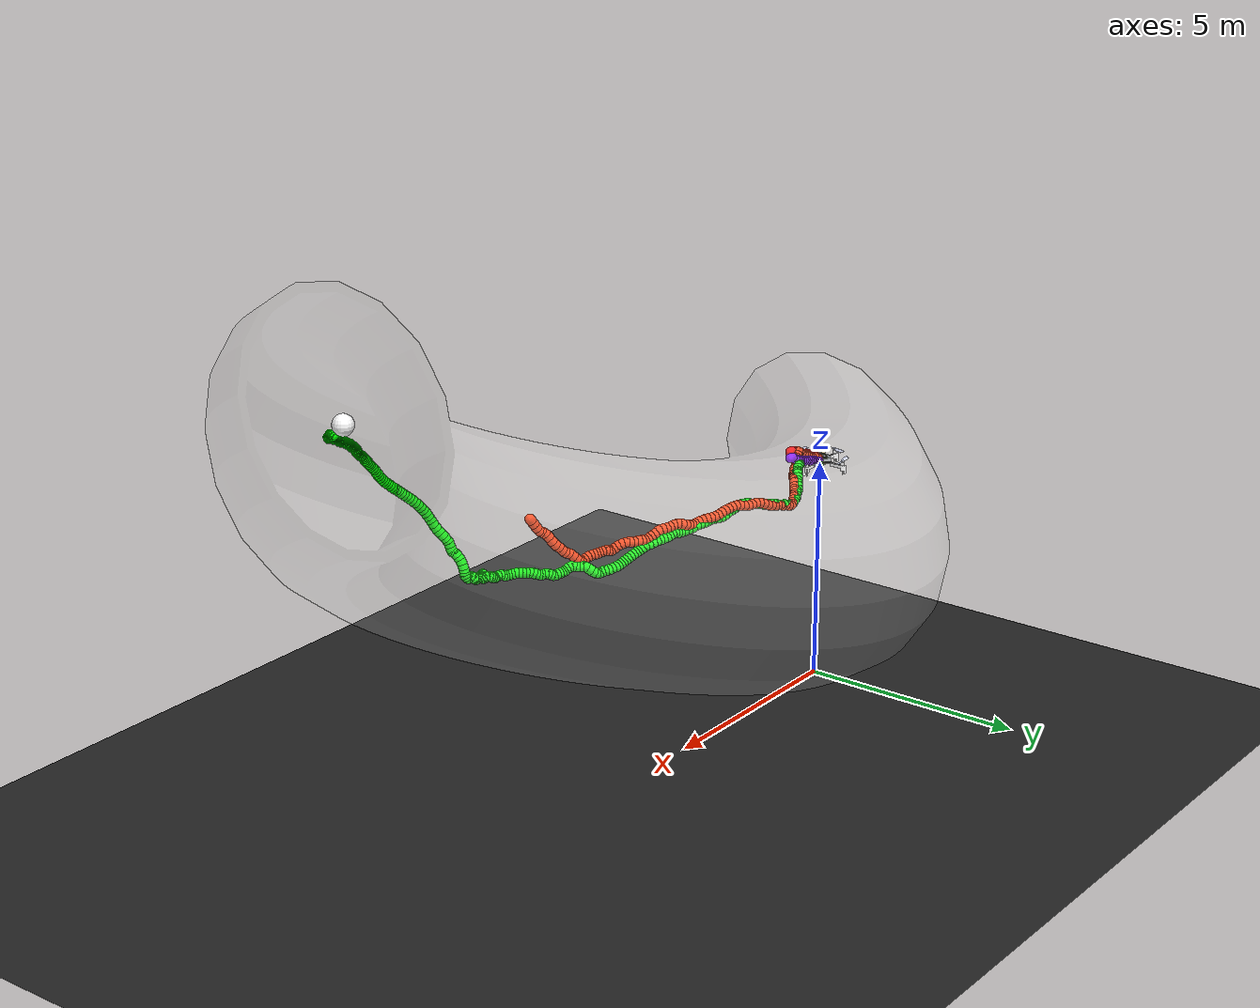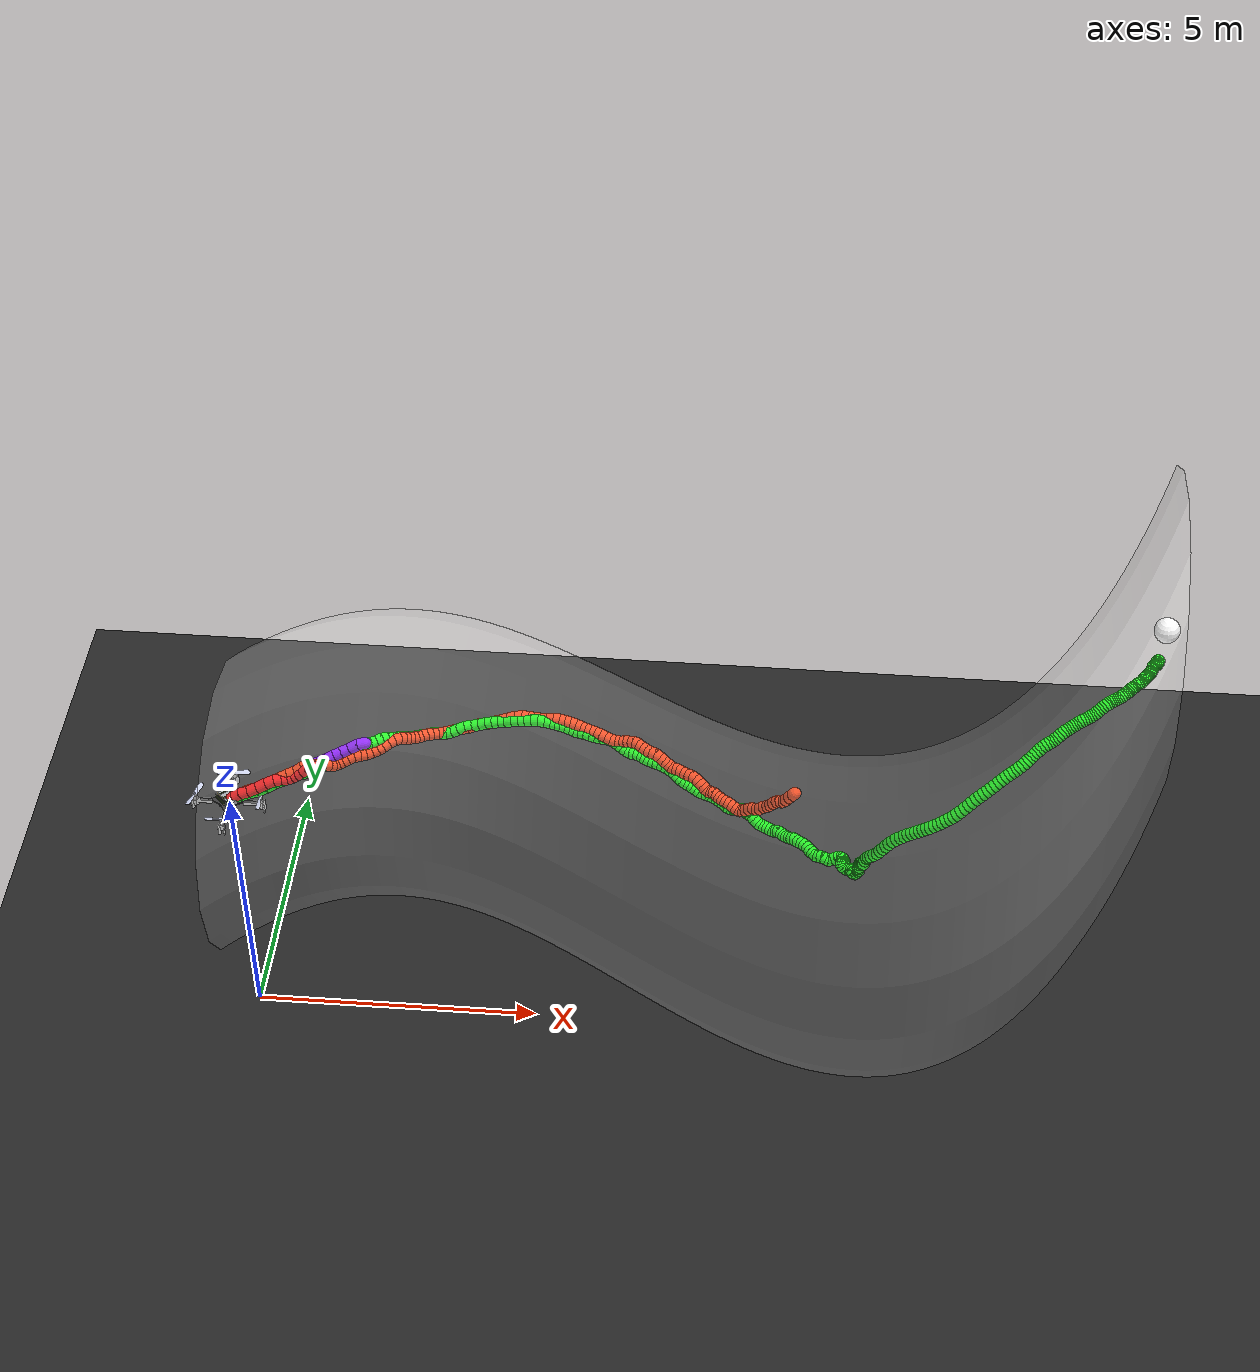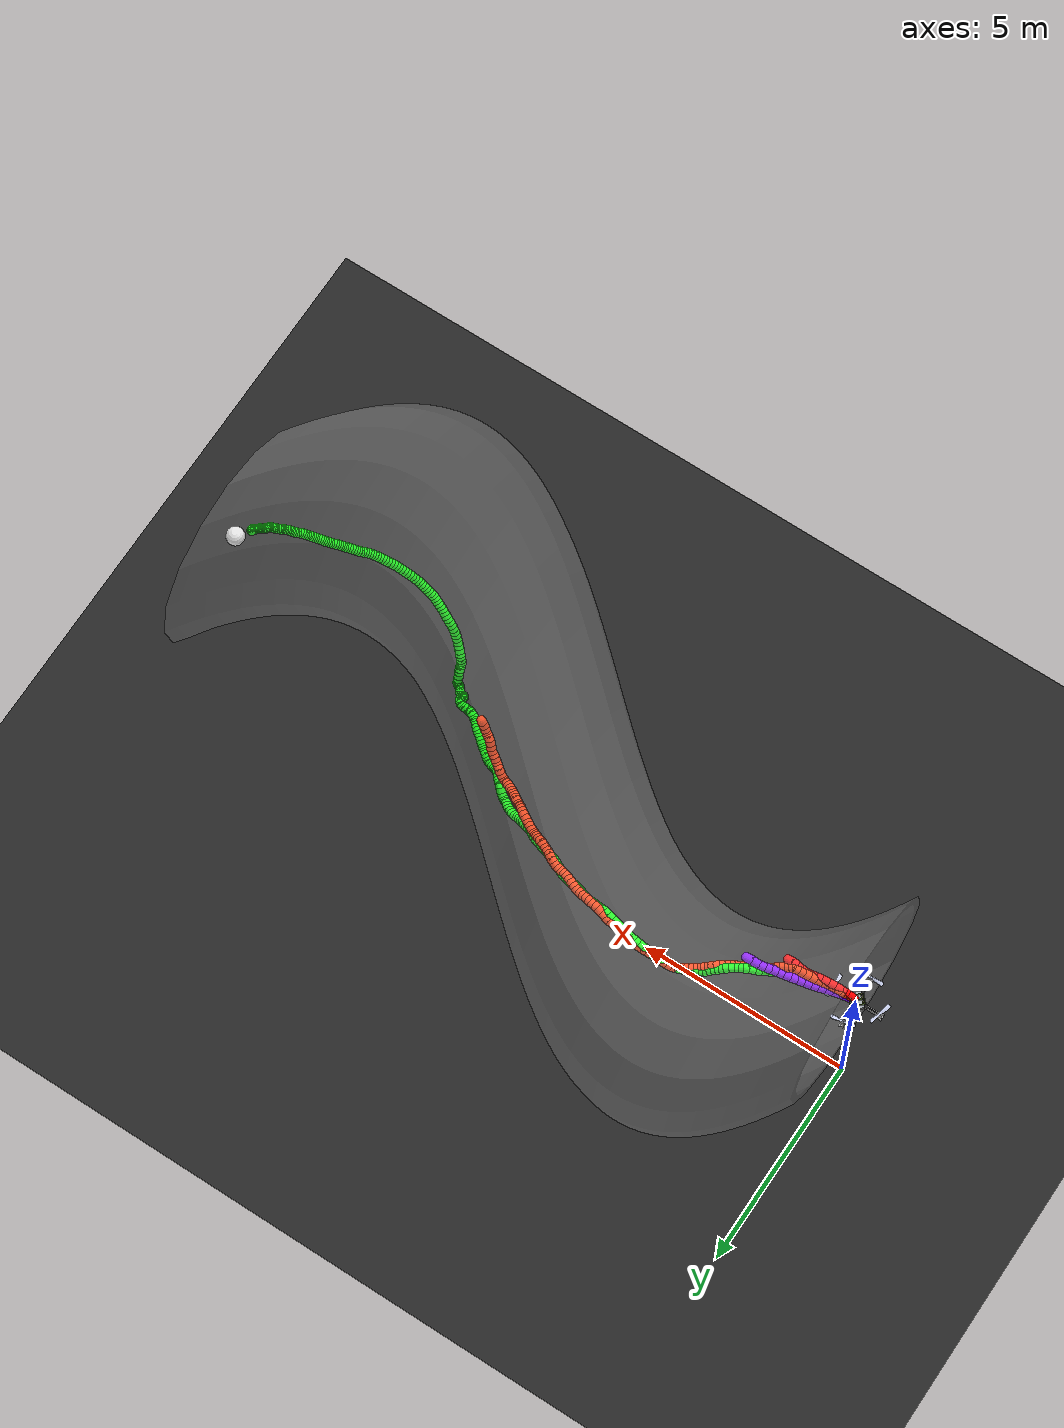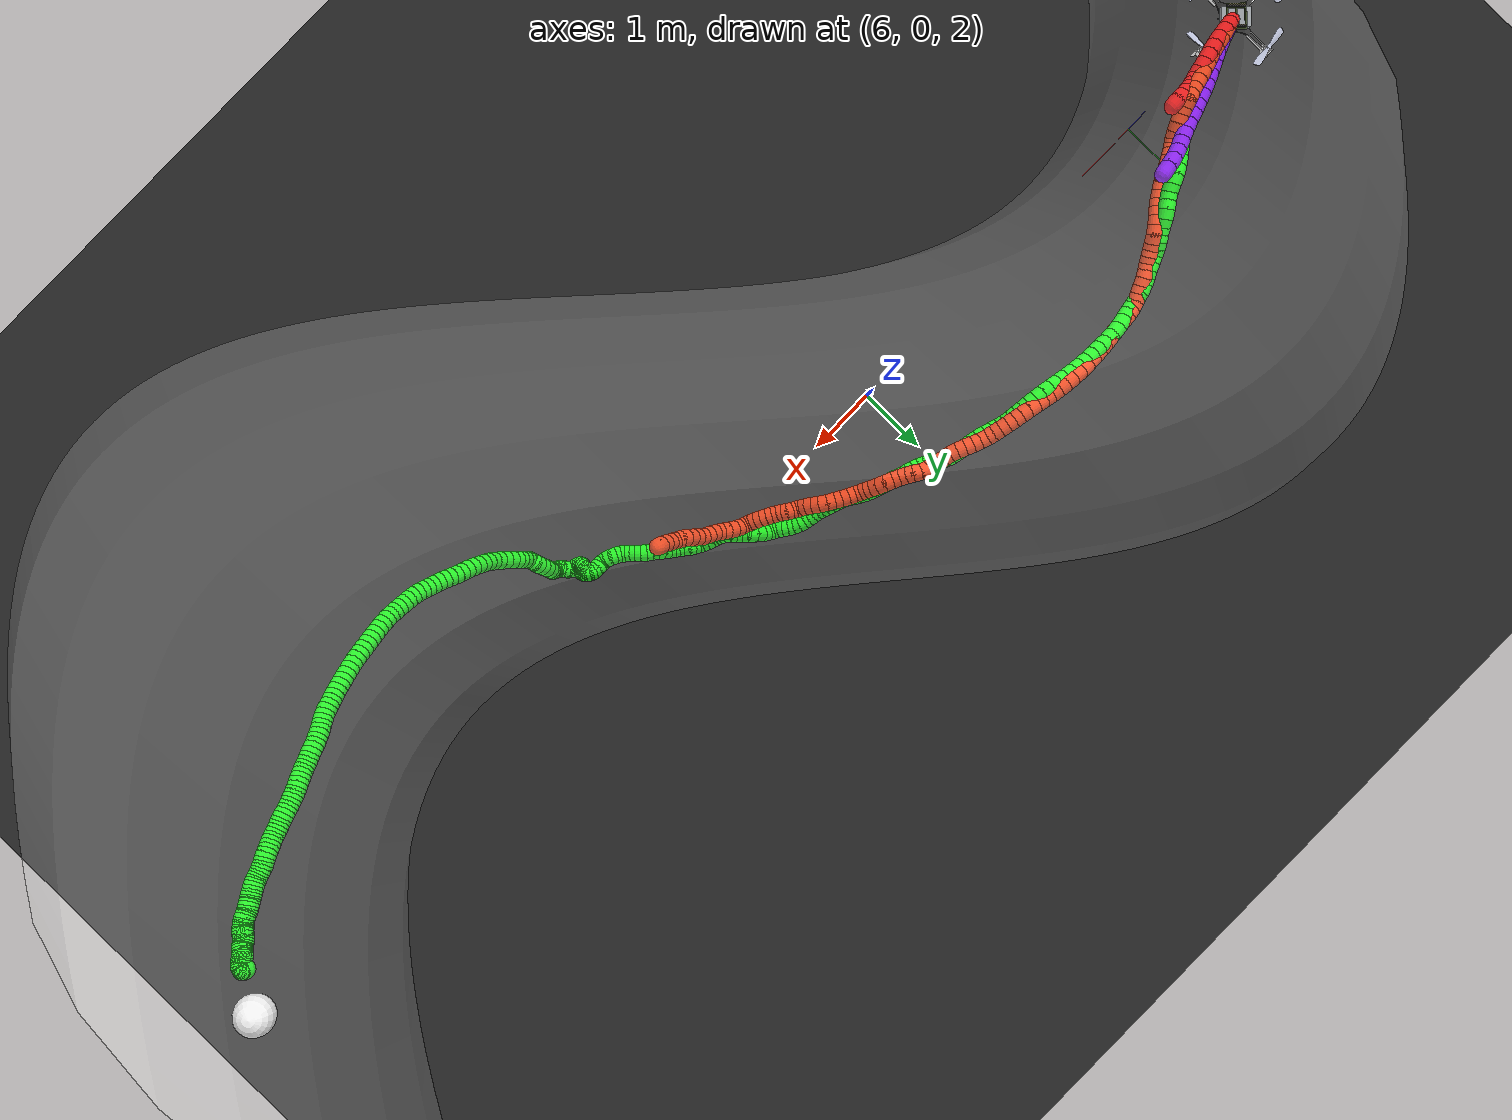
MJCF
<mujoco model="CF2 scene">
  <include file="cf2.xml" />

  <statistic center="0 0 0.1" extent="0.2" meansize=".05" />

  <visual>

    <rgba haze="0.15 0.25 0.35 0" />
    <global azimuth="-20" elevation="-20" ellipsoidinertia="true" />
    <map zfar="1000" />
  </visual>

  <asset>
    <mesh name="tunnel" file="tube_thick.obj" scale="1.0 1.0 1.0" />
    <texture type="skybox" builtin="gradient" rgb1="0.3 0.5 0.7" rgb2="0 0 0" width="512" height="3072" />

    <texture type="2d" name="groundplane" builtin="checker" mark="edge" rgb1="0.1 0.1 0.1" rgb2="0.2 0.2 0.2" markrgb="0.8 0.8 0.8" width="300" height="300" />

    <material name="groundplane" texture="groundplane" texuniform="true" texrepeat="5 5" reflectance="0.1" />
  </asset>

  <worldbody>
    <light diffuse="1 1 1" ambient="1 1 1" pos="0 0 100" dir="0 0 -1" directional="false" castshadow="false" />

    <geom name="floor" size="0 0 0.05" type="plane" material="groundplane" />
    <site name="x_axis" size="0.005" type="cylinder" fromto="0 0 0 1 0 0" rgba="1 0 0 1" />
    <site name="y_axis" size="0.005" type="cylinder" fromto="0 0 0 0 1 0" rgba="0 1 0 1" />
    <site name="z_axis" size="0.005" type="cylinder" fromto="0 0 0 0 0 1" rgba="0 0 1 1" />

    <site name="target" size="0.2" type="sphere" pos="15 0 10" rgba="1 1 1 1" />

    <camera name="cam_aux" pos="-3.429 -18.876 13.649" xyaxes="0.874 -0.486 -0.000 0.179 0.321 0.930" />
    <camera name="cam_traj_1" pos="-7.863 -0.826 23.122" xyaxes="0.020 -1.000 0.000 0.737 0.014 0.676" />
    <camera name="cam_traj_2" pos="7.041 -14.560 20.718" xyaxes="1.000 -0.031 -0.000 0.021 0.691 0.722" />
    <camera name="cam_traj_3" pos="-11.538 -0.602 8.690" xyaxes="0.046 -0.999 -0.000 0.161 0.007 0.987" />

    <body name="tunnel" pos="0.0 0.0 0.0" quat="1 0 0 0">
         <geom name="tunnel" type="mesh" mesh="tunnel" pos="-0.0 0.0 0.029" quat="1 0 0 0" rgba="1 1 1 0.05" />
    </body>

  <body name="trajectory_0" pos="0 0 0"><geom type="capsule" fromto="0.0019727964579132596 0.00018505007084933153 5.03058627781532 0.01699953277119872 0.0016775694669319732 5.073237709097768" size="0.1" rgba="1 0 0 1" /><geom type="capsule" fromto="0.01699953277119872 0.0016775694669319732 5.073237709097768 0.0764289722003477 0.0077504102951051175 5.124588376231838" size="0.1" rgba="1 0 0 1" /><geom type="capsule" fromto="0.0764289722003477 0.0077504102951051175 5.124588376231838 0.19513215021433386 0.01956804778556667 5.1975302654731435" size="0.1" rgba="1 0 0 1" /><geom type="capsule" fromto="0.19513215021433386 0.01956804778556667 5.1975302654731435 0.3369998179194882 0.03442367877139018 5.252899397499029" size="0.1" rgba="1 0 0 1" /><geom type="capsule" fromto="0.3369998179194882 0.03442367877139018 5.252899397499029 0.49265984104185145 0.05803306066817593 5.325665591282086" size="0.1" rgba="1 0 0 1" /><geom type="capsule" fromto="0.49265984104185145 0.05803306066817593 5.325665591282086 0.6418576176913594 0.08893413731175083 5.4059484357789955" size="0.1" rgba="1 0 0 1" /><geom type="capsule" fromto="0.6418576176913594 0.08893413731175083 5.4059484357789955 0.7764405351120481 0.11751552264034945 5.460593773902056" size="0.1" rgba="1 0 0 1" /><geom type="capsule" fromto="0.7764405351120481 0.11751552264034945 5.460593773902056 0.8916818324993118 0.14243238359944077 5.468651086569325" size="0.1" rgba="1 0 0 1" /><geom type="capsule" fromto="0.8916818324993118 0.14243238359944077 5.468651086569325 0.9919036122673954 0.16601870991108258 5.469459630558995" size="0.1" rgba="1 0 0 1" /><geom type="capsule" fromto="0.9919036122673954 0.16601870991108258 5.469459630558995 1.0784990474232141 0.18582009231992175 5.497492872863246" size="0.1" rgba="1 0 0 1" /><geom type="capsule" fromto="1.0784990474232141 0.18582009231992175 5.497492872863246 1.1583839571996752 0.1979993993759248 5.545219517773642" size="0.1" rgba="1 0 0 1" /><geom type="capsule" fromto="1.1583839571996752 0.1979993993759248 5.545219517773642 1.2458296320809106 0.20471804313288205 5.612399515067055" size="0.1" rgba="1 0 0 1" /><geom type="capsule" fromto="1.2458296320809106 0.20471804313288205 5.612399515067055 1.3448071681416909 0.20764430686984575 5.694112389297813" size="0.1" rgba="1 0 0 1" /><geom type="capsule" fromto="1.3448071681416909 0.20764430686984575 5.694112389297813 1.440467025687549 0.20838760387019162 5.730967116373713" size="0.1" rgba="1 0 0 1" /><geom type="capsule" fromto="1.440467025687549 0.20838760387019162 5.730967116373713 1.5372055604677448 0.21307712989498037 5.72800175792511" size="0.1" rgba="1 0 0 1" /></body><body name="trajectory_1" pos="0 0 0"><geom type="capsule" fromto="0.0018071721150837395 0.00035445464952582525 5.023489859848956 0.014547376717637828 0.003091979699008576 5.045566316776575" size="0.1" rgba="0.5 0.0 1.0 1" /><geom type="capsule" fromto="0.014547376717637828 0.003091979699008576 5.045566316776575 0.07661255485763852 0.019501064945579672 5.087633292239033" size="0.1" rgba="0.5 0.0 1.0 1" /><geom type="capsule" fromto="0.07661255485763852 0.019501064945579672 5.087633292239033 0.18887974983262193 0.04951837940775483 5.141485497704365" size="0.1" rgba="0.5 0.0 1.0 1" /><geom type="capsule" fromto="0.18887974983262193 0.04951837940775483 5.141485497704365 0.32683566706490963 0.08900978324353101 5.181606866577063" size="0.1" rgba="0.5 0.0 1.0 1" /><geom type="capsule" fromto="0.32683566706490963 0.08900978324353101 5.181606866577063 0.4802636348271526 0.14189108778117526 5.231036348529384" size="0.1" rgba="0.5 0.0 1.0 1" /><geom type="capsule" fromto="0.4802636348271526 0.14189108778117526 5.231036348529384 0.6274681827980678 0.2014597138442237 5.280749237322678" size="0.1" rgba="0.5 0.0 1.0 1" /><geom type="capsule" fromto="0.6274681827980678 0.2014597138442237 5.280749237322678 0.7683563957678538 0.2587981319381996 5.329568015306759" size="0.1" rgba="0.5 0.0 1.0 1" /><geom type="capsule" fromto="0.7683563957678538 0.2587981319381996 5.329568015306759 0.9087895647317337 0.3107676641331657 5.382725971753927" size="0.1" rgba="0.5 0.0 1.0 1" /><geom type="capsule" fromto="0.9087895647317337 0.3107676641331657 5.382725971753927 1.0517376318277816 0.3584811128443673 5.441341669027419" size="0.1" rgba="0.5 0.0 1.0 1" /><geom type="capsule" fromto="1.0517376318277816 0.3584811128443673 5.441341669027419 1.1890264784259343 0.40236669359767535 5.484141300055087" size="0.1" rgba="0.5 0.0 1.0 1" /><geom type="capsule" fromto="1.1890264784259343 0.40236669359767535 5.484141300055087 1.3279729111372809 0.4445765624935224 5.529318448391913" size="0.1" rgba="0.5 0.0 1.0 1" /><geom type="capsule" fromto="1.3279729111372809 0.4445765624935224 5.529318448391913 1.469741634613172 0.48392889758875224 5.581131923988946" size="0.1" rgba="0.5 0.0 1.0 1" /><geom type="capsule" fromto="1.469741634613172 0.48392889758875224 5.581131923988946 1.6028987947477733 0.5233720513969012 5.62907498968429" size="0.1" rgba="0.5 0.0 1.0 1" /><geom type="capsule" fromto="1.6028987947477733 0.5233720513969012 5.62907498968429 1.7277789410934903 0.5681704525200372 5.682561063448643" size="0.1" rgba="0.5 0.0 1.0 1" /><geom type="capsule" fromto="1.7277789410934903 0.5681704525200372 5.682561063448643 1.8481122433555568 0.6129794784314608 5.726086493330854" size="0.1" rgba="0.5 0.0 1.0 1" /><geom type="capsule" fromto="1.8481122433555568 0.6129794784314608 5.726086493330854 1.9850650757411386 0.6489786990703482 5.787360707957356" size="0.1" rgba="0.5 0.0 1.0 1" /><geom type="capsule" fromto="1.9850650757411386 0.6489786990703482 5.787360707957356 2.135480982759047 0.6715162430498381 5.877207181905166" size="0.1" rgba="0.5 0.0 1.0 1" /><geom type="capsule" fromto="2.135480982759047 0.6715162430498381 5.877207181905166 2.252908720469499 0.6890559096883304 5.899153562140846" size="0.1" rgba="0.5 0.0 1.0 1" /></body><body name="trajectory_2" pos="0 0 0"><geom type="capsule" fromto="0.0016242307066964491 0.00035727284126292657 5.025240836531203 0.016792177813116975 0.0035838782917272127 5.068077347418681" size="0.1" rgba="1 0.2 0.0 1" /><geom type="capsule" fromto="0.016792177813116975 0.0035838782917272127 5.068077347418681 0.06507794690503341 0.011791616971504782 5.102545168872628" size="0.1" rgba="1 0.2 0.0 1" /><geom type="capsule" fromto="0.06507794690503341 0.011791616971504782 5.102545168872628 0.17600153098318522 0.03164271755064546 5.16753624537369" size="0.1" rgba="1 0.2 0.0 1" /><geom type="capsule" fromto="0.17600153098318522 0.03164271755064546 5.16753624537369 0.32722478067976635 0.06061030097704882 5.24559968063181" size="0.1" rgba="1 0.2 0.0 1" /><geom type="capsule" fromto="0.32722478067976635 0.06061030097704882 5.24559968063181 0.4681508263271362 0.08900980247075686 5.282821376171256" size="0.1" rgba="1 0.2 0.0 1" /><geom type="capsule" fromto="0.4681508263271362 0.08900980247075686 5.282821376171256 0.6018157600888904 0.11767093485095181 5.327084009479256" size="0.1" rgba="1 0.2 0.0 1" /><geom type="capsule" fromto="0.6018157600888904 0.11767093485095181 5.327084009479256 0.7402822786519755 0.15044524774542536 5.41260967560658" size="0.1" rgba="1 0.2 0.0 1" /><geom type="capsule" fromto="0.7402822786519755 0.15044524774542536 5.41260967560658 0.8656667919114448 0.1827594041475904 5.466191825755004" size="0.1" rgba="1 0.2 0.0 1" /><geom type="capsule" fromto="0.8656667919114448 0.1827594041475904 5.466191825755004 1.0000742271575636 0.21320986772431977 5.529156459676245" size="0.1" rgba="1 0.2 0.0 1" /><geom type="capsule" fromto="1.0000742271575636 0.21320986772431977 5.529156459676245 1.1309166958522894 0.24163478632838348 5.58000816374289" size="0.1" rgba="1 0.2 0.0 1" /><geom type="capsule" fromto="1.1309166958522894 0.24163478632838348 5.58000816374289 1.2488103382406166 0.2694466236793322 5.662883042841976" size="0.1" rgba="1 0.2 0.0 1" /><geom type="capsule" fromto="1.2488103382406166 0.2694466236793322 5.662883042841976 1.342564037281537 0.29607451788016925 5.709321277438194" size="0.1" rgba="1 0.2 0.0 1" /><geom type="capsule" fromto="1.342564037281537 0.29607451788016925 5.709321277438194 1.418511499548895 0.32198483103521863 5.679278104889069" size="0.1" rgba="1 0.2 0.0 1" /><geom type="capsule" fromto="1.418511499548895 0.32198483103521863 5.679278104889069 1.5008463677522434 0.35533789570155455 5.6520462384423" size="0.1" rgba="1 0.2 0.0 1" /><geom type="capsule" fromto="1.5008463677522434 0.35533789570155455 5.6520462384423 1.5878056039032877 0.39757571087802734 5.623655684157181" size="0.1" rgba="1 0.2 0.0 1" /><geom type="capsule" fromto="1.5878056039032877 0.39757571087802734 5.623655684157181 1.666302889656289 0.4438420000958776 5.57870450509224" size="0.1" rgba="1 0.2 0.0 1" /><geom type="capsule" fromto="1.666302889656289 0.4438420000958776 5.57870450509224 1.7330056734746202 0.49118244411282663 5.53204344336847" size="0.1" rgba="1 0.2 0.0 1" /><geom type="capsule" fromto="1.7330056734746202 0.49118244411282663 5.53204344336847 1.7956577550508948 0.535576608465578 5.523877414556881" size="0.1" rgba="1 0.2 0.0 1" /><geom type="capsule" fromto="1.7956577550508948 0.535576608465578 5.523877414556881 1.8679827067285817 0.5762815142047812 5.54714198520346" size="0.1" rgba="1 0.2 0.0 1" /><geom type="capsule" fromto="1.8679827067285817 0.5762815142047812 5.54714198520346 1.9517918913069394 0.6167259430169639 5.575853768205154" size="0.1" rgba="1 0.2 0.0 1" /><geom type="capsule" fromto="1.9517918913069394 0.6167259430169639 5.575853768205154 2.038902157467931 0.6608764973850116 5.593298757132049" size="0.1" rgba="1 0.2 0.0 1" /><geom type="capsule" fromto="2.038902157467931 0.6608764973850116 5.593298757132049 2.1284173640098354 0.709831470780614 5.587448438459598" size="0.1" rgba="1 0.2 0.0 1" /><geom type="capsule" fromto="2.1284173640098354 0.709831470780614 5.587448438459598 2.2169501855641016 0.7605677327903723 5.559242145740712" size="0.1" rgba="1 0.2 0.0 1" /><geom type="capsule" fromto="2.2169501855641016 0.7605677327903723 5.559242145740712 2.3112102748219234 0.8169199101810714 5.5614641626859065" size="0.1" rgba="1 0.2 0.0 1" /><geom type="capsule" fromto="2.3112102748219234 0.8169199101810714 5.5614641626859065 2.40127291748281 0.8754002663322565 5.569014345120183" size="0.1" rgba="1 0.2 0.0 1" /><geom type="capsule" fromto="2.40127291748281 0.8754002663322565 5.569014345120183 2.4875064212119073 0.9364565188115707 5.584957554248743" size="0.1" rgba="1 0.2 0.0 1" /><geom type="capsule" fromto="2.4875064212119073 0.9364565188115707 5.584957554248743 2.5747721851727676 1.001745473799322 5.621791601263369" size="0.1" rgba="1 0.2 0.0 1" /><geom type="capsule" fromto="2.5747721851727676 1.001745473799322 5.621791601263369 2.65861637798802 1.0642421756426634 5.631029485779322" size="0.1" rgba="1 0.2 0.0 1" /><geom type="capsule" fromto="2.65861637798802 1.0642421756426634 5.631029485779322 2.7411138218613287 1.1245784246029351 5.622998117316388" size="0.1" rgba="1 0.2 0.0 1" /><geom type="capsule" fromto="2.7411138218613287 1.1245784246029351 5.622998117316388 2.8136458446482657 1.1800812371873701 5.579181506806972" size="0.1" rgba="1 0.2 0.0 1" /><geom type="capsule" fromto="2.8136458446482657 1.1800812371873701 5.579181506806972 2.8808387233562134 1.2272831784517444 5.540600999252269" size="0.1" rgba="1 0.2 0.0 1" /><geom type="capsule" fromto="2.8808387233562134 1.2272831784517444 5.540600999252269 2.9460517205397223 1.2682071365661216 5.522883477218278" size="0.1" rgba="1 0.2 0.0 1" /><geom type="capsule" fromto="2.9460517205397223 1.2682071365661216 5.522883477218278 3.0099617979020588 1.31073154631683 5.494507364225115" size="0.1" rgba="1 0.2 0.0 1" /><geom type="capsule" fromto="3.0099617979020588 1.31073154631683 5.494507364225115 3.0815509552020006 1.3589520281451197 5.484540081544132" size="0.1" rgba="1 0.2 0.0 1" /><geom type="capsule" fromto="3.0815509552020006 1.3589520281451197 5.484540081544132 3.1617993903104114 1.406021451782459 5.4822482853178265" size="0.1" rgba="1 0.2 0.0 1" /><geom type="capsule" fromto="3.1617993903104114 1.406021451782459 5.4822482853178265 3.244704450776487 1.448343516317241 5.461847636371677" size="0.1" rgba="1 0.2 0.0 1" /><geom type="capsule" fromto="3.244704450776487 1.448343516317241 5.461847636371677 3.3276558356664885 1.489820941288449 5.443806455548776" size="0.1" rgba="1 0.2 0.0 1" /><geom type="capsule" fromto="3.3276558356664885 1.489820941288449 5.443806455548776 3.4073448099199375 1.5295863373490803 5.426697739153552" size="0.1" rgba="1 0.2 0.0 1" /><geom type="capsule" fromto="3.4073448099199375 1.5295863373490803 5.426697739153552 3.4935380315692743 1.5597853122671557 5.419922366060234" size="0.1" rgba="1 0.2 0.0 1" /><geom type="capsule" fromto="3.4935380315692743 1.5597853122671557 5.419922366060234 3.60463244564459 1.5749952801672735 5.453905540618287" size="0.1" rgba="1 0.2 0.0 1" /><geom type="capsule" fromto="3.60463244564459 1.5749952801672735 5.453905540618287 3.7325640119812458 1.5816359115523224 5.504700672452823" size="0.1" rgba="1 0.2 0.0 1" /><geom type="capsule" fromto="3.7325640119812458 1.5816359115523224 5.504700672452823 3.850083433560304 1.588427130504364 5.533291559684574" size="0.1" rgba="1 0.2 0.0 1" /><geom type="capsule" fromto="3.850083433560304 1.588427130504364 5.533291559684574 3.9625700580019876 1.599174928223456 5.5783735645183" size="0.1" rgba="1 0.2 0.0 1" /><geom type="capsule" fromto="3.9625700580019876 1.599174928223456 5.5783735645183 4.067230835111724 1.6095394765053506 5.609014302170815" size="0.1" rgba="1 0.2 0.0 1" /><geom type="capsule" fromto="4.067230835111724 1.6095394765053506 5.609014302170815 4.171890940346022 1.6155674688338924 5.623693563580451" size="0.1" rgba="1 0.2 0.0 1" /><geom type="capsule" fromto="4.171890940346022 1.6155674688338924 5.623693563580451 4.2934765243901 1.6176929795776511 5.668305854217339" size="0.1" rgba="1 0.2 0.0 1" /><geom type="capsule" fromto="4.2934765243901 1.6176929795776511 5.668305854217339 4.419902530393039 1.6167829223956516 5.7176279335245095" size="0.1" rgba="1 0.2 0.0 1" /><geom type="capsule" fromto="4.419902530393039 1.6167829223956516 5.7176279335245095 4.55404674898675 1.6100784589623782 5.781771847339537" size="0.1" rgba="1 0.2 0.0 1" /><geom type="capsule" fromto="4.55404674898675 1.6100784589623782 5.781771847339537 4.68240202902296 1.5986458450993475 5.837876008735576" size="0.1" rgba="1 0.2 0.0 1" /><geom type="capsule" fromto="4.68240202902296 1.5986458450993475 5.837876008735576 4.7976702611906425 1.584358974221217 5.869985262824092" size="0.1" rgba="1 0.2 0.0 1" /><geom type="capsule" fromto="4.7976702611906425 1.584358974221217 5.869985262824092 4.903078518351056 1.5692603074590965 5.875188975130719" size="0.1" rgba="1 0.2 0.0 1" /><geom type="capsule" fromto="4.903078518351056 1.5692603074590965 5.875188975130719 5.007457546887881 1.5518438466244664 5.877084085718385" size="0.1" rgba="1 0.2 0.0 1" /><geom type="capsule" fromto="5.007457546887881 1.5518438466244664 5.877084085718385 5.115559516999508 1.528886041532279 5.8907459765075" size="0.1" rgba="1 0.2 0.0 1" /><geom type="capsule" fromto="5.115559516999508 1.528886041532279 5.8907459765075 5.23252134127328 1.5019843509274633 5.9278310665144085" size="0.1" rgba="1 0.2 0.0 1" /><geom type="capsule" fromto="5.23252134127328 1.5019843509274633 5.9278310665144085 5.345171982166391 1.4785058433263893 5.960061648124492" size="0.1" rgba="1 0.2 0.0 1" /><geom type="capsule" fromto="5.345171982166391 1.4785058433263893 5.960061648124492 5.442390969864802 1.4603501807592605 5.9590552389691265" size="0.1" rgba="1 0.2 0.0 1" /><geom type="capsule" fromto="5.442390969864802 1.4603501807592605 5.9590552389691265 5.5346885068898874 1.443008370937544 5.949667980546088" size="0.1" rgba="1 0.2 0.0 1" /><geom type="capsule" fromto="5.5346885068898874 1.443008370937544 5.949667980546088 5.626135603291774 1.4246341984446305 5.9400957532096985" size="0.1" rgba="1 0.2 0.0 1" /><geom type="capsule" fromto="5.626135603291774 1.4246341984446305 5.9400957532096985 5.7151233602751965 1.4061955293742519 5.921407425031522" size="0.1" rgba="1 0.2 0.0 1" /><geom type="capsule" fromto="5.7151233602751965 1.4061955293742519 5.921407425031522 5.801174329835579 1.386815406849964 5.89293278287863" size="0.1" rgba="1 0.2 0.0 1" /><geom type="capsule" fromto="5.801174329835579 1.386815406849964 5.89293278287863 5.887958106777882 1.3637752860997612 5.873238068884671" size="0.1" rgba="1 0.2 0.0 1" /><geom type="capsule" fromto="5.887958106777882 1.3637752860997612 5.873238068884671 5.976359447849797 1.3345377129209899 5.866356856855762" size="0.1" rgba="1 0.2 0.0 1" /><geom type="capsule" fromto="5.976359447849797 1.3345377129209899 5.866356856855762 6.06410174842795 1.2995365846694318 5.861068800998261" size="0.1" rgba="1 0.2 0.0 1" /><geom type="capsule" fromto="6.06410174842795 1.2995365846694318 5.861068800998261 6.151435540912381 1.2615977103667306 5.854859526399462" size="0.1" rgba="1 0.2 0.0 1" /><geom type="capsule" fromto="6.151435540912381 1.2615977103667306 5.854859526399462 6.238310309042901 1.2262095482924693 5.84171078609308" size="0.1" rgba="1 0.2 0.0 1" /><geom type="capsule" fromto="6.238310309042901 1.2262095482924693 5.84171078609308 6.324083865501767 1.1982528191537227 5.821479897412174" size="0.1" rgba="1 0.2 0.0 1" /><geom type="capsule" fromto="6.324083865501767 1.1982528191537227 5.821479897412174 6.40930906146631 1.178572728631368 5.809296512767536" size="0.1" rgba="1 0.2 0.0 1" /><geom type="capsule" fromto="6.40930906146631 1.178572728631368 5.809296512767536 6.4918991405930955 1.1641935195629112 5.816236199469627" size="0.1" rgba="1 0.2 0.0 1" /><geom type="capsule" fromto="6.4918991405930955 1.1641935195629112 5.816236199469627 6.573919849766287 1.1466830604806073 5.845241351726314" size="0.1" rgba="1 0.2 0.0 1" /><geom type="capsule" fromto="6.573919849766287 1.1466830604806073 5.845241351726314 6.656795009206265 1.119929902947843 5.873926759811006" size="0.1" rgba="1 0.2 0.0 1" /><geom type="capsule" fromto="6.656795009206265 1.119929902947843 5.873926759811006 6.734125020997047 1.0820376168675396 5.904031865970198" size="0.1" rgba="1 0.2 0.0 1" /><geom type="capsule" fromto="6.734125020997047 1.0820376168675396 5.904031865970198 6.800256044432322 1.0402150489585322 5.905858343408738" size="0.1" rgba="1 0.2 0.0 1" /><geom type="capsule" fromto="6.800256044432322 1.0402150489585322 5.905858343408738 6.865610409185712 1.000342457008332 5.883025008993923" size="0.1" rgba="1 0.2 0.0 1" /><geom type="capsule" fromto="6.865610409185712 1.000342457008332 5.883025008993923 6.9388240475831795 0.9615884743030279 5.8632844425371395" size="0.1" rgba="1 0.2 0.0 1" /><geom type="capsule" fromto="6.9388240475831795 0.9615884743030279 5.8632844425371395 7.01887802822784 0.923044299796602 5.8515727229766625" size="0.1" rgba="1 0.2 0.0 1" /><geom type="capsule" fromto="7.01887802822784 0.923044299796602 5.8515727229766625 7.103482197998484 0.8861573893896347 5.851278807668758" size="0.1" rgba="1 0.2 0.0 1" /><geom type="capsule" fromto="7.103482197998484 0.8861573893896347 5.851278807668758 7.179551616046154 0.8524786159385916 5.815367740774389" size="0.1" rgba="1 0.2 0.0 1" /><geom type="capsule" fromto="7.179551616046154 0.8524786159385916 5.815367740774389 7.245376618125558 0.8202457098674308 5.767782657273866" size="0.1" rgba="1 0.2 0.0 1" /><geom type="capsule" fromto="7.245376618125558 0.8202457098674308 5.767782657273866 7.304454829949599 0.7905750332880024 5.737136215683552" size="0.1" rgba="1 0.2 0.0 1" /><geom type="capsule" fromto="7.304454829949599 0.7905750332880024 5.737136215683552 7.361037657022653 0.7623368903480221 5.7006352968648875" size="0.1" rgba="1 0.2 0.0 1" /><geom type="capsule" fromto="7.361037657022653 0.7623368903480221 5.7006352968648875 7.427715037334346 0.7312914393924569 5.691406786780552" size="0.1" rgba="1 0.2 0.0 1" /><geom type="capsule" fromto="7.427715037334346 0.7312914393924569 5.691406786780552 7.502151015385965 0.6945636075611535 5.702757537265521" size="0.1" rgba="1 0.2 0.0 1" /><geom type="capsule" fromto="7.502151015385965 0.6945636075611535 5.702757537265521 7.574577271036616 0.6533389027876062 5.696820153435637" size="0.1" rgba="1 0.2 0.0 1" /><geom type="capsule" fromto="7.574577271036616 0.6533389027876062 5.696820153435637 7.651062757357083 0.6093339912183711 5.694370599264193" size="0.1" rgba="1 0.2 0.0 1" /><geom type="capsule" fromto="7.651062757357083 0.6093339912183711 5.694370599264193 7.7317128640896415 0.5618720638462409 5.708560232360654" size="0.1" rgba="1 0.2 0.0 1" /><geom type="capsule" fromto="7.7317128640896415 0.5618720638462409 5.708560232360654 7.8034570072227645 0.5135937798306125 5.697506284180835" size="0.1" rgba="1 0.2 0.0 1" /><geom type="capsule" fromto="7.8034570072227645 0.5135937798306125 5.697506284180835 7.86414712073867 0.4675170546952716 5.667538368240765" size="0.1" rgba="1 0.2 0.0 1" /><geom type="capsule" fromto="7.86414712073867 0.4675170546952716 5.667538368240765 7.9206408028433755 0.42614854832843274 5.635069070266618" size="0.1" rgba="1 0.2 0.0 1" /><geom type="capsule" fromto="7.9206408028433755 0.42614854832843274 5.635069070266618 7.974703530905389 0.3914754733742265 5.590272342352884" size="0.1" rgba="1 0.2 0.0 1" /><geom type="capsule" fromto="7.974703530905389 0.3914754733742265 5.590272342352884 8.025289788129495 0.361817691193683 5.569556616216855" size="0.1" rgba="1 0.2 0.0 1" /><geom type="capsule" fromto="8.025289788129495 0.361817691193683 5.569556616216855 8.076274138818068 0.3328183963649934 5.583359268296424" size="0.1" rgba="1 0.2 0.0 1" /><geom type="capsule" fromto="8.076274138818068 0.3328183963649934 5.583359268296424 8.126599521996907 0.3016610419208043 5.591010703600376" size="0.1" rgba="1 0.2 0.0 1" /><geom type="capsule" fromto="8.126599521996907 0.3016610419208043 5.591010703600376 8.173148734932758 0.268333030497553 5.577449709464876" size="0.1" rgba="1 0.2 0.0 1" /><geom type="capsule" fromto="8.173148734932758 0.268333030497553 5.577449709464876 8.221013027450914 0.23540966486938594 5.562498325287376" size="0.1" rgba="1 0.2 0.0 1" /><geom type="capsule" fromto="8.221013027450914 0.23540966486938594 5.562498325287376 8.274981507867205 0.20402781960002447 5.551002733867967" size="0.1" rgba="1 0.2 0.0 1" /><geom type="capsule" fromto="8.274981507867205 0.20402781960002447 5.551002733867967 8.333695703859483 0.17152036962250017 5.5421904230851045" size="0.1" rgba="1 0.2 0.0 1" /><geom type="capsule" fromto="8.333695703859483 0.17152036962250017 5.5421904230851045 8.393246725246613 0.1393878894117273 5.529218439965589" size="0.1" rgba="1 0.2 0.0 1" /><geom type="capsule" fromto="8.393246725246613 0.1393878894117273 5.529218439965589 8.453003660063855 0.11040218221378234 5.5048909318613175" size="0.1" rgba="1 0.2 0.0 1" /><geom type="capsule" fromto="8.453003660063855 0.11040218221378234 5.5048909318613175 8.512406038404974 0.08449284187156411 5.478617547149719" size="0.1" rgba="1 0.2 0.0 1" /><geom type="capsule" fromto="8.512406038404974 0.08449284187156411 5.478617547149719 8.57247289184411 0.062046058087883244 5.465179292225573" size="0.1" rgba="1 0.2 0.0 1" /><geom type="capsule" fromto="8.57247289184411 0.062046058087883244 5.465179292225573 8.637262644456335 0.03669449268802879 5.4991291892856715" size="0.1" rgba="1 0.2 0.0 1" /><geom type="capsule" fromto="8.637262644456335 0.03669449268802879 5.4991291892856715 8.70424337245949 0.00199566547271713 5.568226347360947" size="0.1" rgba="1 0.2 0.0 1" /><geom type="capsule" fromto="8.70424337245949 0.00199566547271713 5.568226347360947 8.769879496792328 -0.03979927582322768 5.642242548467266" size="0.1" rgba="1 0.2 0.0 1" /><geom type="capsule" fromto="8.769879496792328 -0.03979927582322768 5.642242548467266 8.828222380116042 -0.08144571345189003 5.6720718549371245" size="0.1" rgba="1 0.2 0.0 1" /><geom type="capsule" fromto="8.828222380116042 -0.08144571345189003 5.6720718549371245 8.884416165731597 -0.12010256467969463 5.713964177138538" size="0.1" rgba="1 0.2 0.0 1" /><geom type="capsule" fromto="8.884416165731597 -0.12010256467969463 5.713964177138538 8.947166906712814 -0.1531208600427742 5.795049651379743" size="0.1" rgba="1 0.2 0.0 1" /><geom type="capsule" fromto="8.947166906712814 -0.1531208600427742 5.795049651379743 9.010873239442583 -0.18376968193338478 5.850810165953785" size="0.1" rgba="1 0.2 0.0 1" /><geom type="capsule" fromto="9.010873239442583 -0.18376968193338478 5.850810165953785 9.068490707877125 -0.22407121160075555 5.928645785307671" size="0.1" rgba="1 0.2 0.0 1" /><geom type="capsule" fromto="9.068490707877125 -0.22407121160075555 5.928645785307671 9.11676383934948 -0.2706361281922799 6.017876606654177" size="0.1" rgba="1 0.2 0.0 1" /><geom type="capsule" fromto="9.11676383934948 -0.2706361281922799 6.017876606654177 9.16745300774453 -0.31351791086236647 6.104811319477405" size="0.1" rgba="1 0.2 0.0 1" /><geom type="capsule" fromto="9.16745300774453 -0.31351791086236647 6.104811319477405 9.220365929492951 -0.34937368177950073 6.1599343724238755" size="0.1" rgba="1 0.2 0.0 1" /><geom type="capsule" fromto="9.220365929492951 -0.34937368177950073 6.1599343724238755 9.270121584137605 -0.37709575988653676 6.17866178149529" size="0.1" rgba="1 0.2 0.0 1" /><geom type="capsule" fromto="9.270121584137605 -0.37709575988653676 6.17866178149529 9.319912562516278 -0.4030155713088363 6.2389902982175585" size="0.1" rgba="1 0.2 0.0 1" /><geom type="capsule" fromto="9.319912562516278 -0.4030155713088363 6.2389902982175585 9.372464919452616 -0.43161688310997615 6.327600323677753" size="0.1" rgba="1 0.2 0.0 1" /><geom type="capsule" fromto="9.372464919452616 -0.43161688310997615 6.327600323677753 9.424948808703903 -0.45487448570197403 6.417660803286492" size="0.1" rgba="1 0.2 0.0 1" /><geom type="capsule" fromto="9.424948808703903 -0.45487448570197403 6.417660803286492 9.471810715829012 -0.4710506803187078 6.484917668395276" size="0.1" rgba="1 0.2 0.0 1" /></body><body name="trajectory_3" pos="0 0 0"><geom type="capsule" fromto="0.0012853595546936593 0.00047027934031070723 5.013283614304885 0.014320140048435539 0.0050479653705119655 5.031109401533253" size="0.1" rgba="0 1 0.0 1" /><geom type="capsule" fromto="0.014320140048435539 0.0050479653705119655 5.031109401533253 0.07044156455876667 0.019501336843949946 5.0655241527247155" size="0.1" rgba="0 1 0.0 1" /><geom type="capsule" fromto="0.07044156455876667 0.019501336843949946 5.0655241527247155 0.18905273629593777 0.043307146330075916 5.131095809090465" size="0.1" rgba="0 1 0.0 1" /><geom type="capsule" fromto="0.18905273629593777 0.043307146330075916 5.131095809090465 0.3324227043228154 0.06920457783752437 5.181594380862981" size="0.1" rgba="0 1 0.0 1" /><geom type="capsule" fromto="0.3324227043228154 0.06920457783752437 5.181594380862981 0.47441368721917954 0.09621750043521152 5.212262039523513" size="0.1" rgba="0 1 0.0 1" /><geom type="capsule" fromto="0.47441368721917954 0.09621750043521152 5.212262039523513 0.6234043451026282 0.13208580829039573 5.272291521315724" size="0.1" rgba="0 1 0.0 1" /><geom type="capsule" fromto="0.6234043451026282 0.13208580829039573 5.272291521315724 0.7649198268359869 0.17480595422133702 5.340476582608986" size="0.1" rgba="0 1 0.0 1" /><geom type="capsule" fromto="0.7649198268359869 0.17480595422133702 5.340476582608986 0.88765346686393 0.21682683458195892 5.3759221204298715" size="0.1" rgba="0 1 0.0 1" /><geom type="capsule" fromto="0.88765346686393 0.21682683458195892 5.3759221204298715 1.0145313326666103 0.26136879443507605 5.410701777998895" size="0.1" rgba="0 1 0.0 1" /><geom type="capsule" fromto="1.0145313326666103 0.26136879443507605 5.410701777998895 1.1489817576778785 0.307893260023797 5.449848350718764" size="0.1" rgba="0 1 0.0 1" /><geom type="capsule" fromto="1.1489817576778785 0.307893260023797 5.449848350718764 1.2699959795191598 0.3507298606047964 5.454170608363493" size="0.1" rgba="0 1 0.0 1" /><geom type="capsule" fromto="1.2699959795191598 0.3507298606047964 5.454170608363493 1.3861913397560763 0.3929128574111028 5.460892155032756" size="0.1" rgba="0 1 0.0 1" /><geom type="capsule" fromto="1.3861913397560763 0.3929128574111028 5.460892155032756 1.496504709875158 0.43988680346568854 5.509290303588491" size="0.1" rgba="0 1 0.0 1" /><geom type="capsule" fromto="1.496504709875158 0.43988680346568854 5.509290303588491 1.5863871900158981 0.49076761629786914 5.54265692409006" size="0.1" rgba="0 1 0.0 1" /><geom type="capsule" fromto="1.5863871900158981 0.49076761629786914 5.54265692409006 1.6739154376313652 0.5479120036146577 5.56276242009826" size="0.1" rgba="0 1 0.0 1" /><geom type="capsule" fromto="1.6739154376313652 0.5479120036146577 5.56276242009826 1.7805186417331205 0.6193964239873305 5.621937599389062" size="0.1" rgba="0 1 0.0 1" /><geom type="capsule" fromto="1.7805186417331205 0.6193964239873305 5.621937599389062 1.8824695019959323 0.69046450439656 5.654841771319888" size="0.1" rgba="0 1 0.0 1" /><geom type="capsule" fromto="1.8824695019959323 0.69046450439656 5.654841771319888 1.9891768180557539 0.7549733628861904 5.692622501821689" size="0.1" rgba="0 1 0.0 1" /><geom type="capsule" fromto="1.9891768180557539 0.7549733628861904 5.692622501821689 2.0991953454807293 0.809452806399863 5.72706469846556" size="0.1" rgba="0 1 0.0 1" /><geom type="capsule" fromto="2.0991953454807293 0.809452806399863 5.72706469846556 2.19557072496153 0.8542998385862836 5.7166319539052814" size="0.1" rgba="0 1 0.0 1" /><geom type="capsule" fromto="2.19557072496153 0.8542998385862836 5.7166319539052814 2.284068153373448 0.899142674487456 5.692419570251989" size="0.1" rgba="0 1 0.0 1" /><geom type="capsule" fromto="2.284068153373448 0.899142674487456 5.692419570251989 2.370657348108244 0.9540868594714961 5.690626315442958" size="0.1" rgba="0 1 0.0 1" /><geom type="capsule" fromto="2.370657348108244 0.9540868594714961 5.690626315442958 2.456012154077368 1.0153574630438378 5.697653286327407" size="0.1" rgba="0 1 0.0 1" /><geom type="capsule" fromto="2.456012154077368 1.0153574630438378 5.697653286327407 2.535971271448708 1.0717395450611225 5.67065806088946" size="0.1" rgba="0 1 0.0 1" /><geom type="capsule" fromto="2.535971271448708 1.0717395450611225 5.67065806088946 2.6119982420988785 1.1206358476504363 5.627738629939149" size="0.1" rgba="0 1 0.0 1" /><geom type="capsule" fromto="2.6119982420988785 1.1206358476504363 5.627738629939149 2.6821238170612145 1.1664084100460024 5.599244072378168" size="0.1" rgba="0 1 0.0 1" /><geom type="capsule" fromto="2.6821238170612145 1.1664084100460024 5.599244072378168 2.7446069942895623 1.213303572756715 5.574690287239894" size="0.1" rgba="0 1 0.0 1" /><geom type="capsule" fromto="2.7446069942895623 1.213303572756715 5.574690287239894 2.805426458777354 1.258425111268267 5.530160853954514" size="0.1" rgba="0 1 0.0 1" /><geom type="capsule" fromto="2.805426458777354 1.258425111268267 5.530160853954514 2.875116517463497 1.2989118657855734 5.487732728518108" size="0.1" rgba="0 1 0.0 1" /><geom type="capsule" fromto="2.875116517463497 1.2989118657855734 5.487732728518108 2.960894376224521 1.3373006998252057 5.483002474064678" size="0.1" rgba="0 1 0.0 1" /><geom type="capsule" fromto="2.960894376224521 1.3373006998252057 5.483002474064678 3.0449042755864646 1.37851595250864 5.4745120286261395" size="0.1" rgba="0 1 0.0 1" /><geom type="capsule" fromto="3.0449042755864646 1.37851595250864 5.4745120286261395 3.120082584939899 1.4216801619511124 5.449414533562812" size="0.1" rgba="0 1 0.0 1" /><geom type="capsule" fromto="3.120082584939899 1.4216801619511124 5.449414533562812 3.20341013654604 1.4612441636925664 5.450447531222437" size="0.1" rgba="0 1 0.0 1" /><geom type="capsule" fromto="3.20341013654604 1.4612441636925664 5.450447531222437 3.2947084475276265 1.4936551959511524 5.4492724039547396" size="0.1" rgba="0 1 0.0 1" /><geom type="capsule" fromto="3.2947084475276265 1.4936551959511524 5.4492724039547396 3.3822742405827397 1.5201087095277377 5.423797225708948" size="0.1" rgba="0 1 0.0 1" /><geom type="capsule" fromto="3.3822742405827397 1.5201087095277377 5.423797225708948 3.470784099156863 1.5375055205935335 5.41356299093114" size="0.1" rgba="0 1 0.0 1" /><geom type="capsule" fromto="3.470784099156863 1.5375055205935335 5.41356299093114 3.56814990879444 1.5512085311457642 5.443393186767296" size="0.1" rgba="0 1 0.0 1" /><geom type="capsule" fromto="3.56814990879444 1.5512085311457642 5.443393186767296 3.6775834262647304 1.5691004925615553 5.490088241913491" size="0.1" rgba="0 1 0.0 1" /><geom type="capsule" fromto="3.6775834262647304 1.5691004925615553 5.490088241913491 3.801989317787098 1.5856923280275335 5.542201777159132" size="0.1" rgba="0 1 0.0 1" /><geom type="capsule" fromto="3.801989317787098 1.5856923280275335 5.542201777159132 3.9225162708412125 1.5962026210966214 5.568362147914935" size="0.1" rgba="0 1 0.0 1" /><geom type="capsule" fromto="3.9225162708412125 1.5962026210966214 5.568362147914935 4.044583318094686 1.5955895784529424 5.606591332476915" size="0.1" rgba="0 1 0.0 1" /><geom type="capsule" fromto="4.044583318094686 1.5955895784529424 5.606591332476915 4.163129007900079 1.5879183724630648 5.658157381811024" size="0.1" rgba="0 1 0.0 1" /><geom type="capsule" fromto="4.163129007900079 1.5879183724630648 5.658157381811024 4.271758988233045 1.58176591624074 5.691498841716204" size="0.1" rgba="0 1 0.0 1" /><geom type="capsule" fromto="4.271758988233045 1.58176591624074 5.691498841716204 4.380829664274427 1.5767930701667434 5.716643391147755" size="0.1" rgba="0 1 0.0 1" /><geom type="capsule" fromto="4.380829664274427 1.5767930701667434 5.716643391147755 4.494560082521928 1.565985984624405 5.742263220341499" size="0.1" rgba="0 1 0.0 1" /><geom type="capsule" fromto="4.494560082521928 1.565985984624405 5.742263220341499 4.619213822912443 1.5473306982746111 5.790782277008472" size="0.1" rgba="0 1 0.0 1" /><geom type="capsule" fromto="4.619213822912443 1.5473306982746111 5.790782277008472 4.738611011023173 1.5273387315540075 5.828018673764754" size="0.1" rgba="0 1 0.0 1" /><geom type="capsule" fromto="4.738611011023173 1.5273387315540075 5.828018673764754 4.851270136628162 1.5056965778199667 5.850449418085789" size="0.1" rgba="0 1 0.0 1" /><geom type="capsule" fromto="4.851270136628162 1.5056965778199667 5.850449418085789 4.969541848413545 1.482268208265379 5.888261574270945" size="0.1" rgba="0 1 0.0 1" /><geom type="capsule" fromto="4.969541848413545 1.482268208265379 5.888261574270945 5.0829081081662615 1.461598447121547 5.912937967250372" size="0.1" rgba="0 1 0.0 1" /><geom type="capsule" fromto="5.0829081081662615 1.461598447121547 5.912937967250372 5.186085342463987 1.4461021557684763 5.9152725871975855" size="0.1" rgba="0 1 0.0 1" /><geom type="capsule" fromto="5.186085342463987 1.4461021557684763 5.9152725871975855 5.279478342949308 1.4357856291478943 5.906904547517201" size="0.1" rgba="0 1 0.0 1" /><geom type="capsule" fromto="5.279478342949308 1.4357856291478943 5.906904547517201 5.362744119114053 1.427218686011689 5.885731148842143" size="0.1" rgba="0 1 0.0 1" /><geom type="capsule" fromto="5.362744119114053 1.427218686011689 5.885731148842143 5.446045800653232 1.4177440293034551 5.870681132115739" size="0.1" rgba="0 1 0.0 1" /><geom type="capsule" fromto="5.446045800653232 1.4177440293034551 5.870681132115739 5.5323646622992895 1.4079496941899474 5.857753522480356" size="0.1" rgba="0 1 0.0 1" /><geom type="capsule" fromto="5.5323646622992895 1.4079496941899474 5.857753522480356 5.614782070405464 1.3963112406591327 5.824708961379177" size="0.1" rgba="0 1 0.0 1" /><geom type="capsule" fromto="5.614782070405464 1.3963112406591327 5.824708961379177 5.696491875005756 1.376808627845909 5.799635175745899" size="0.1" rgba="0 1 0.0 1" /><geom type="capsule" fromto="5.696491875005756 1.376808627845909 5.799635175745899 5.781757966387723 1.3484300303531394 5.799161119145286" size="0.1" rgba="0 1 0.0 1" /><geom type="capsule" fromto="5.781757966387723 1.3484300303531394 5.799161119145286 5.873093268552207 1.318396274491166 5.808656809504275" size="0.1" rgba="0 1 0.0 1" /><geom type="capsule" fromto="5.873093268552207 1.318396274491166 5.808656809504275 5.9642642624230096 1.2930149910297328 5.804247668266089" size="0.1" rgba="0 1 0.0 1" /><geom type="capsule" fromto="5.9642642624230096 1.2930149910297328 5.804247668266089 6.052620417322947 1.2756309370170462 5.790775556820336" size="0.1" rgba="0 1 0.0 1" /><geom type="capsule" fromto="6.052620417322947 1.2756309370170462 5.790775556820336 6.140606945463323 1.2624010040256732 5.7861392973188535" size="0.1" rgba="0 1 0.0 1" /><geom type="capsule" fromto="6.140606945463323 1.2624010040256732 5.7861392973188535 6.229532547215699 1.2461091636758315 5.791720625196338" size="0.1" rgba="0 1 0.0 1" /><geom type="capsule" fromto="6.229532547215699 1.2461091636758315 5.791720625196338 6.315795874856431 1.2245306352662069 5.7887029148924" size="0.1" rgba="0 1 0.0 1" /><geom type="capsule" fromto="6.315795874856431 1.2245306352662069 5.7887029148924 6.394386700334637 1.1951616989395575 5.764748525817891" size="0.1" rgba="0 1 0.0 1" /><geom type="capsule" fromto="6.394386700334637 1.1951616989395575 5.764748525817891 6.468185499540562 1.1565288161722624 5.738642869998028" size="0.1" rgba="0 1 0.0 1" /><geom type="capsule" fromto="6.468185499540562 1.1565288161722624 5.738642869998028 6.537366709105285 1.1125837608168043 5.722247315473538" size="0.1" rgba="0 1 0.0 1" /><geom type="capsule" fromto="6.537366709105285 1.1125837608168043 5.722247315473538 6.602445762853487 1.0704577591380553 5.701204291201918" size="0.1" rgba="0 1 0.0 1" /><geom type="capsule" fromto="6.602445762853487 1.0704577591380553 5.701204291201918 6.672901279435501 1.035328606119307 5.693577357736813" size="0.1" rgba="0 1 0.0 1" /><geom type="capsule" fromto="6.672901279435501 1.035328606119307 5.693577357736813 6.743049162329453 1.0113718380963337 5.707833859998446" size="0.1" rgba="0 1 0.0 1" /><geom type="capsule" fromto="6.743049162329453 1.0113718380963337 5.707833859998446 6.802137263746081 0.9939671322073246 5.705083944797465" size="0.1" rgba="0 1 0.0 1" /><geom type="capsule" fromto="6.802137263746081 0.9939671322073246 5.705083944797465 6.859378816504023 0.9755010707516942 5.686566203489542" size="0.1" rgba="0 1 0.0 1" /><geom type="capsule" fromto="6.859378816504023 0.9755010707516942 5.686566203489542 6.924111439992232 0.9523843735810097 5.666618744623862" size="0.1" rgba="0 1 0.0 1" /><geom type="capsule" fromto="6.924111439992232 0.9523843735810097 5.666618744623862 6.998490691722804 0.9259877574097988 5.650974262630583" size="0.1" rgba="0 1 0.0 1" /><geom type="capsule" fromto="6.998490691722804 0.9259877574097988 5.650974262630583 7.077191655934562 0.9000486765660425 5.640646558667137" size="0.1" rgba="0 1 0.0 1" /><geom type="capsule" fromto="7.077191655934562 0.9000486765660425 5.640646558667137 7.156230058276215 0.8746365041832206 5.636503142195299" size="0.1" rgba="0 1 0.0 1" /><geom type="capsule" fromto="7.156230058276215 0.8746365041832206 5.636503142195299 7.233759279485944 0.8484313641309236 5.620707647836825" size="0.1" rgba="0 1 0.0 1" /><geom type="capsule" fromto="7.233759279485944 0.8484313641309236 5.620707647836825 7.308967672074701 0.8177552203705137 5.6002400550741624" size="0.1" rgba="0 1 0.0 1" /><geom type="capsule" fromto="7.308967672074701 0.8177552203705137 5.6002400550741624 7.379265313657744 0.7781111986519614 5.588206228561372" size="0.1" rgba="0 1 0.0 1" /><geom type="capsule" fromto="7.379265313657744 0.7781111986519614 5.588206228561372 7.440364285106929 0.7363381017432487 5.549215169609405" size="0.1" rgba="0 1 0.0 1" /><geom type="capsule" fromto="7.440364285106929 0.7363381017432487 5.549215169609405 7.498065635196446 0.6999212032030055 5.5095927734429" size="0.1" rgba="0 1 0.0 1" /><geom type="capsule" fromto="7.498065635196446 0.6999212032030055 5.5095927734429 7.55664341956195 0.670193672701184 5.481850550214689" size="0.1" rgba="0 1 0.0 1" /><geom type="capsule" fromto="7.55664341956195 0.670193672701184 5.481850550214689 7.616415878000519 0.6478791003377449 5.4543222846224895" size="0.1" rgba="0 1 0.0 1" /><geom type="capsule" fromto="7.616415878000519 0.6478791003377449 5.4543222846224895 7.676579106463314 0.6304967628083307 5.432906892450077" size="0.1" rgba="0 1 0.0 1" /><geom type="capsule" fromto="7.676579106463314 0.6304967628083307 5.432906892450077 7.734381328063129 0.6109344949663152 5.408773166597203" size="0.1" rgba="0 1 0.0 1" /><geom type="capsule" fromto="7.734381328063129 0.6109344949663152 5.408773166597203 7.790544661794439 0.5885054561551705 5.376495069472317" size="0.1" rgba="0 1 0.0 1" /><geom type="capsule" fromto="7.790544661794439 0.5885054561551705 5.376495069472317 7.850345156048979 0.5692751443498798 5.348946323741599" size="0.1" rgba="0 1 0.0 1" /><geom type="capsule" fromto="7.850345156048979 0.5692751443498798 5.348946323741599 7.915130384366121 0.5577862534341884 5.328844901971434" size="0.1" rgba="0 1 0.0 1" /><geom type="capsule" fromto="7.915130384366121 0.5577862534341884 5.328844901971434 7.980323348645969 0.5487797819940239 5.307302073198862" size="0.1" rgba="0 1 0.0 1" /><geom type="capsule" fromto="7.980323348645969 0.5487797819940239 5.307302073198862 8.044749273788982 0.5345895005039615 5.295546109400312" size="0.1" rgba="0 1 0.0 1" /><geom type="capsule" fromto="8.044749273788982 0.5345895005039615 5.295546109400312 8.109992676665586 0.5122421637091074 5.286187774673868" size="0.1" rgba="0 1 0.0 1" /><geom type="capsule" fromto="8.109992676665586 0.5122421637091074 5.286187774673868 8.174264236118264 0.48261037761581105 5.266456213759932" size="0.1" rgba="0 1 0.0 1" /><geom type="capsule" fromto="8.174264236118264 0.48261037761581105 5.266456213759932 8.233673521774064 0.44711070234808603 5.2553972562956766" size="0.1" rgba="0 1 0.0 1" /><geom type="capsule" fromto="8.233673521774064 0.44711070234808603 5.2553972562956766 8.28567168465211 0.4090693332553852 5.248031743431805" size="0.1" rgba="0 1 0.0 1" /><geom type="capsule" fromto="8.28567168465211 0.4090693332553852 5.248031743431805 8.334630143932445 0.37365101491735114 5.225058156529853" size="0.1" rgba="0 1 0.0 1" /><geom type="capsule" fromto="8.334630143932445 0.37365101491735114 5.225058156529853 8.388160454938713 0.344510522402945 5.215526971270021" size="0.1" rgba="0 1 0.0 1" /><geom type="capsule" fromto="8.388160454938713 0.344510522402945 5.215526971270021 8.445426996420078 0.3139420519204106 5.234418653328291" size="0.1" rgba="0 1 0.0 1" /><geom type="capsule" fromto="8.445426996420078 0.3139420519204106 5.234418653328291 8.505780352313792 0.26849517109985366 5.287083339313003" size="0.1" rgba="0 1 0.0 1" /><geom type="capsule" fromto="8.505780352313792 0.26849517109985366 5.287083339313003 8.571009055444698 0.21088911822484885 5.359783714759391" size="0.1" rgba="0 1 0.0 1" /><geom type="capsule" fromto="8.571009055444698 0.21088911822484885 5.359783714759391 8.631635779562975 0.15482938815632258 5.393020057118192" size="0.1" rgba="0 1 0.0 1" /><geom type="capsule" fromto="8.631635779562975 0.15482938815632258 5.393020057118192 8.68277365065277 0.10310375102830459 5.384945591175701" size="0.1" rgba="0 1 0.0 1" /><geom type="capsule" fromto="8.68277365065277 0.10310375102830459 5.384945591175701 8.728738840399513 0.052741182526529026 5.399091776944285" size="0.1" rgba="0 1 0.0 1" /><geom type="capsule" fromto="8.728738840399513 0.052741182526529026 5.399091776944285 8.773550906596862 0.005922928369021682 5.411327771848506" size="0.1" rgba="0 1 0.0 1" /><geom type="capsule" fromto="8.773550906596862 0.005922928369021682 5.411327771848506 8.818449942264591 -0.03434345301716425 5.382544946797536" size="0.1" rgba="0 1 0.0 1" /><geom type="capsule" fromto="8.818449942264591 -0.03434345301716425 5.382544946797536 8.86730421495154 -0.06558192446864468 5.343681081420352" size="0.1" rgba="0 1 0.0 1" /><geom type="capsule" fromto="8.86730421495154 -0.06558192446864468 5.343681081420352 8.918674534426465 -0.08708927749381357 5.317318079188049" size="0.1" rgba="0 1 0.0 1" /><geom type="capsule" fromto="8.918674534426465 -0.08708927749381357 5.317318079188049 8.972167064106806 -0.10506299449518691 5.306807927322927" size="0.1" rgba="0 1 0.0 1" /><geom type="capsule" fromto="8.972167064106806 -0.10506299449518691 5.306807927322927 9.030105713796734 -0.12586646693285822 5.299979275022605" size="0.1" rgba="0 1 0.0 1" /><geom type="capsule" fromto="9.030105713796734 -0.12586646693285822 5.299979275022605 9.087562403290843 -0.15107906520376568 5.281132381173714" size="0.1" rgba="0 1 0.0 1" /><geom type="capsule" fromto="9.087562403290843 -0.15107906520376568 5.281132381173714 9.141801376190966 -0.1809152094599241 5.285600443989492" size="0.1" rgba="0 1 0.0 1" /><geom type="capsule" fromto="9.141801376190966 -0.1809152094599241 5.285600443989492 9.19210301332263 -0.21088552718501985 5.314642422301078" size="0.1" rgba="0 1 0.0 1" /><geom type="capsule" fromto="9.19210301332263 -0.21088552718501985 5.314642422301078 9.238100718220432 -0.2423984919200437 5.334612443486429" size="0.1" rgba="0 1 0.0 1" /><geom type="capsule" fromto="9.238100718220432 -0.2423984919200437 5.334612443486429 9.281433295056724 -0.2778844802746072 5.331822601432883" size="0.1" rgba="0 1 0.0 1" /><geom type="capsule" fromto="9.281433295056724 -0.2778844802746072 5.331822601432883 9.325660239464234 -0.31456651594745644 5.329994840819013" size="0.1" rgba="0 1 0.0 1" /><geom type="capsule" fromto="9.325660239464234 -0.31456651594745644 5.329994840819013 9.37451257714785 -0.35017425578530986 5.339591446131251" size="0.1" rgba="0 1 0.0 1" /><geom type="capsule" fromto="9.37451257714785 -0.35017425578530986 5.339591446131251 9.425886285415984 -0.38746850139389183 5.35971116129518" size="0.1" rgba="0 1 0.0 1" /><geom type="capsule" fromto="9.425886285415984 -0.38746850139389183 5.35971116129518 9.475935856364426 -0.42765019428043205 5.392452675120094" size="0.1" rgba="0 1 0.0 1" /><geom type="capsule" fromto="9.475935856364426 -0.42765019428043205 5.392452675120094 9.524524767017672 -0.46861524237794816 5.3999181666144045" size="0.1" rgba="0 1 0.0 1" /><geom type="capsule" fromto="9.524524767017672 -0.46861524237794816 5.3999181666144045 9.57847688735663 -0.5097862457742307 5.401360747113876" size="0.1" rgba="0 1 0.0 1" /><geom type="capsule" fromto="9.57847688735663 -0.5097862457742307 5.401360747113876 9.636285381009042 -0.5516544958526529 5.409222325704218" size="0.1" rgba="0 1 0.0 1" /><geom type="capsule" fromto="9.636285381009042 -0.5516544958526529 5.409222325704218 9.68764385038216 -0.5965629460297038 5.412313442666814" size="0.1" rgba="0 1 0.0 1" /><geom type="capsule" fromto="9.68764385038216 -0.5965629460297038 5.412313442666814 9.731998720266956 -0.6419819360086944 5.4044975417746155" size="0.1" rgba="0 1 0.0 1" /><geom type="capsule" fromto="9.731998720266956 -0.6419819360086944 5.4044975417746155 9.773671570449633 -0.6845914435669327 5.39156839246748" size="0.1" rgba="0 1 0.0 1" /><geom type="capsule" fromto="9.773671570449633 -0.6845914435669327 5.39156839246748 9.816101691045711 -0.7247806519879423 5.380152018510966" size="0.1" rgba="0 1 0.0 1" /><geom type="capsule" fromto="9.816101691045711 -0.7247806519879423 5.380152018510966 9.862156155503383 -0.7628078152277482 5.372362030841846" size="0.1" rgba="0 1 0.0 1" /><geom type="capsule" fromto="9.862156155503383 -0.7628078152277482 5.372362030841846 9.916425286889766 -0.7948064137044099 5.390893813654234" size="0.1" rgba="0 1 0.0 1" /><geom type="capsule" fromto="9.916425286889766 -0.7948064137044099 5.390893813654234 9.974205646884974 -0.8200819669626674 5.403623158419371" size="0.1" rgba="0 1 0.0 1" /><geom type="capsule" fromto="9.974205646884974 -0.8200819669626674 5.403623158419371 10.028435309421875 -0.8392090071759968 5.389520395699723" size="0.1" rgba="0 1 0.0 1" /><geom type="capsule" fromto="10.028435309421875 -0.8392090071759968 5.389520395699723 10.079888044106411 -0.8492539940378828 5.374279207524094" size="0.1" rgba="0 1 0.0 1" /><geom type="capsule" fromto="10.079888044106411 -0.8492539940378828 5.374279207524094 10.13490163716438 -0.848264637385224 5.398146430249362" size="0.1" rgba="0 1 0.0 1" /><geom type="capsule" fromto="10.13490163716438 -0.848264637385224 5.398146430249362 10.188920567755021 -0.8438953579549102 5.432617687489014" size="0.1" rgba="0 1 0.0 1" /><geom type="capsule" fromto="10.188920567755021 -0.8438953579549102 5.432617687489014 10.233435465469455 -0.847020391686348 5.444953763939986" size="0.1" rgba="0 1 0.0 1" /><geom type="capsule" fromto="10.233435465469455 -0.847020391686348 5.444953763939986 10.27113306076534 -0.8627119708105564 5.462424817155609" size="0.1" rgba="0 1 0.0 1" /><geom type="capsule" fromto="10.27113306076534 -0.8627119708105564 5.462424817155609 10.302875370217626 -0.886108520017998 5.4614018511576985" size="0.1" rgba="0 1 0.0 1" /><geom type="capsule" fromto="10.302875370217626 -0.886108520017998 5.4614018511576985 10.325981703243649 -0.9112948728019018 5.433414290448277" size="0.1" rgba="0 1 0.0 1" /><geom type="capsule" fromto="10.325981703243649 -0.9112948728019018 5.433414290448277 10.33610959294911 -0.9326222000168041 5.428022214457907" size="0.1" rgba="0 1 0.0 1" /><geom type="capsule" fromto="10.33610959294911 -0.9326222000168041 5.428022214457907 10.331978811607037 -0.9467840949045458 5.4407136992879215" size="0.1" rgba="0 1 0.0 1" /><geom type="capsule" fromto="10.331978811607037 -0.9467840949045458 5.4407136992879215 10.318148053727048 -0.9554674071430778 5.459704820867776" size="0.1" rgba="0 1 0.0 1" /><geom type="capsule" fromto="10.318148053727048 -0.9554674071430778 5.459704820867776 10.300508771310868 -0.9627617395322445 5.464765368946335" size="0.1" rgba="0 1 0.0 1" /><geom type="capsule" fromto="10.300508771310868 -0.9627617395322445 5.464765368946335 10.285125581213215 -0.9721836723730317 5.469418673944786" size="0.1" rgba="0 1 0.0 1" /><geom type="capsule" fromto="10.285125581213215 -0.9721836723730317 5.469418673944786 10.279859331268021 -0.9858191245886099 5.484570088238192" size="0.1" rgba="0 1 0.0 1" /><geom type="capsule" fromto="10.279859331268021 -0.9858191245886099 5.484570088238192 10.283688319850542 -1.003030996792487 5.470477952169843" size="0.1" rgba="0 1 0.0 1" /><geom type="capsule" fromto="10.283688319850542 -1.003030996792487 5.470477952169843 10.29554303528042 -1.0202177163960942 5.449721803538948" size="0.1" rgba="0 1 0.0 1" /><geom type="capsule" fromto="10.29554303528042 -1.0202177163960942 5.449721803538948 10.315104219386876 -1.0316920732341097 5.436973715231139" size="0.1" rgba="0 1 0.0 1" /><geom type="capsule" fromto="10.315104219386876 -1.0316920732341097 5.436973715231139 10.342360972145269 -1.0378173459961593 5.417471896067149" size="0.1" rgba="0 1 0.0 1" /><geom type="capsule" fromto="10.342360972145269 -1.0378173459961593 5.417471896067149 10.37443164511636 -1.0440138667100363 5.3964146840502805" size="0.1" rgba="0 1 0.0 1" /><geom type="capsule" fromto="10.37443164511636 -1.0440138667100363 5.3964146840502805 10.405327234880849 -1.055821368143249 5.397246249416648" size="0.1" rgba="0 1 0.0 1" /><geom type="capsule" fromto="10.405327234880849 -1.055821368143249 5.397246249416648 10.433682982093124 -1.082024518388896 5.438348753498598" size="0.1" rgba="0 1 0.0 1" /><geom type="capsule" fromto="10.433682982093124 -1.082024518388896 5.438348753498598 10.459753436429738 -1.117313292387249 5.4572567091605455" size="0.1" rgba="0 1 0.0 1" /><geom type="capsule" fromto="10.459753436429738 -1.117313292387249 5.4572567091605455 10.484399617249094 -1.1509911225282963 5.423758501422473" size="0.1" rgba="0 1 0.0 1" /><geom type="capsule" fromto="10.484399617249094 -1.1509911225282963 5.423758501422473 10.515487158689742 -1.1734599095537577 5.432737299790488" size="0.1" rgba="0 1 0.0 1" /><geom type="capsule" fromto="10.515487158689742 -1.1734599095537577 5.432737299790488 10.548708559872102 -1.1838602082093193 5.478476809336593" size="0.1" rgba="0 1 0.0 1" /><geom type="capsule" fromto="10.548708559872102 -1.1838602082093193 5.478476809336593 10.566457590780027 -1.1914874825221602 5.524774033695753" size="0.1" rgba="0 1 0.0 1" /><geom type="capsule" fromto="10.566457590780027 -1.1914874825221602 5.524774033695753 10.568222924087573 -1.198641348948068 5.567300559603926" size="0.1" rgba="0 1 0.0 1" /><geom type="capsule" fromto="10.568222924087573 -1.198641348948068 5.567300559603926 10.567053823462967 -1.2135459326305913 5.627399994597955" size="0.1" rgba="0 1 0.0 1" /><geom type="capsule" fromto="10.567053823462967 -1.2135459326305913 5.627399994597955 10.572045895737078 -1.2442112079835956 5.720845202041701" size="0.1" rgba="0 1 0.0 1" /><geom type="capsule" fromto="10.572045895737078 -1.2442112079835956 5.720845202041701 10.583140773574815 -1.283028847850981 5.805306783134602" size="0.1" rgba="0 1 0.0 1" /><geom type="capsule" fromto="10.583140773574815 -1.283028847850981 5.805306783134602 10.59821023542968 -1.3243713300692044 5.861743504262327" size="0.1" rgba="0 1 0.0 1" /><geom type="capsule" fromto="10.59821023542968 -1.3243713300692044 5.861743504262327 10.61058310076639 -1.3702670873403722 5.918438852582884" size="0.1" rgba="0 1 0.0 1" /><geom type="capsule" fromto="10.61058310076639 -1.3702670873403722 5.918438852582884 10.618938789195935 -1.4144116174122836 5.935992898033661" size="0.1" rgba="0 1 0.0 1" /><geom type="capsule" fromto="10.618938789195935 -1.4144116174122836 5.935992898033661 10.630872881698664 -1.4487044912672313 5.960610928937348" size="0.1" rgba="0 1 0.0 1" /><geom type="capsule" fromto="10.630872881698664 -1.4487044912672313 5.960610928937348 10.648222998645654 -1.4723094072141878 6.053439079285758" size="0.1" rgba="0 1 0.0 1" /><geom type="capsule" fromto="10.648222998645654 -1.4723094072141878 6.053439079285758 10.667807958596491 -1.4926317122261816 6.140300648683695" size="0.1" rgba="0 1 0.0 1" /><geom type="capsule" fromto="10.667807958596491 -1.4926317122261816 6.140300648683695 10.691995978171274 -1.514640940104301 6.189159200435891" size="0.1" rgba="0 1 0.0 1" /><geom type="capsule" fromto="10.691995978171274 -1.514640940104301 6.189159200435891 10.727506484684662 -1.5492202886632869 6.2506428010707715" size="0.1" rgba="0 1 0.0 1" /><geom type="capsule" fromto="10.727506484684662 -1.5492202886632869 6.2506428010707715 10.773618932682755 -1.5937798996782746 6.335072268733134" size="0.1" rgba="0 1 0.0 1" /><geom type="capsule" fromto="10.773618932682755 -1.5937798996782746 6.335072268733134 10.821638834355543 -1.6358674634381911 6.413881645976345" size="0.1" rgba="0 1 0.0 1" /><geom type="capsule" fromto="10.821638834355543 -1.6358674634381911 6.413881645976345 10.8648911122684 -1.6718679545398454 6.500227225275614" size="0.1" rgba="0 1 0.0 1" /><geom type="capsule" fromto="10.8648911122684 -1.6718679545398454 6.500227225275614 10.903604699578388 -1.7000472774560726 6.590020224792977" size="0.1" rgba="0 1 0.0 1" /><geom type="capsule" fromto="10.903604699578388 -1.7000472774560726 6.590020224792977 10.943591561285926 -1.7208575952533558 6.667800282781753" size="0.1" rgba="0 1 0.0 1" /><geom type="capsule" fromto="10.943591561285926 -1.7208575952533558 6.667800282781753 10.988089265072919 -1.7392863784304888 6.74517753382001" size="0.1" rgba="0 1 0.0 1" /><geom type="capsule" fromto="10.988089265072919 -1.7392863784304888 6.74517753382001 11.036188053489438 -1.7584937354044639 6.823790880845725" size="0.1" rgba="0 1 0.0 1" /><geom type="capsule" fromto="11.036188053489438 -1.7584937354044639 6.823790880845725 11.087122001662577 -1.7759064209011322 6.893368313684309" size="0.1" rgba="0 1 0.0 1" /><geom type="capsule" fromto="11.087122001662577 -1.7759064209011322 6.893368313684309 11.14160816870934 -1.79085249655826 6.954452421225911" size="0.1" rgba="0 1 0.0 1" /><geom type="capsule" fromto="11.14160816870934 -1.79085249655826 6.954452421225911 11.198335799488914 -1.806961727411132 7.011705095061679" size="0.1" rgba="0 1 0.0 1" /><geom type="capsule" fromto="11.198335799488914 -1.806961727411132 7.011705095061679 11.254187290849849 -1.8275466726761722 7.071786350224492" size="0.1" rgba="0 1 0.0 1" /><geom type="capsule" fromto="11.254187290849849 -1.8275466726761722 7.071786350224492 11.30816502849907 -1.849294333466121 7.124937526866497" size="0.1" rgba="0 1 0.0 1" /><geom type="capsule" fromto="11.30816502849907 -1.849294333466121 7.124937526866497 11.363031926790603 -1.868125035173085 7.175590393927348" size="0.1" rgba="0 1 0.0 1" /><geom type="capsule" fromto="11.363031926790603 -1.868125035173085 7.175590393927348 11.418518152083752 -1.883884650386851 7.223625819966235" size="0.1" rgba="0 1 0.0 1" /><geom type="capsule" fromto="11.418518152083752 -1.883884650386851 7.223625819966235 11.472726448717955 -1.8991032259915597 7.268122961745168" size="0.1" rgba="0 1 0.0 1" /><geom type="capsule" fromto="11.472726448717955 -1.8991032259915597 7.268122961745168 11.525209919886786 -1.9153999443620766 7.315593143894397" size="0.1" rgba="0 1 0.0 1" /><geom type="capsule" fromto="11.525209919886786 -1.9153999443620766 7.315593143894397 11.577176607494229 -1.9295893626086627 7.360660151583023" size="0.1" rgba="0 1 0.0 1" /><geom type="capsule" fromto="11.577176607494229 -1.9295893626086627 7.360660151583023 11.63145332132855 -1.9388103647623973 7.405769046643539" size="0.1" rgba="0 1 0.0 1" /><geom type="capsule" fromto="11.63145332132855 -1.9388103647623973 7.405769046643539 11.687940151810489 -1.9435403753808014 7.448598870296069" size="0.1" rgba="0 1 0.0 1" /><geom type="capsule" fromto="11.687940151810489 -1.9435403753808014 7.448598870296069 11.745425308940668 -1.9452448387025831 7.494565693740949" size="0.1" rgba="0 1 0.0 1" /><geom type="capsule" fromto="11.745425308940668 -1.9452448387025831 7.494565693740949 11.801634650455057 -1.9460104625416583 7.54438644191205" size="0.1" rgba="0 1 0.0 1" /><geom type="capsule" fromto="11.801634650455057 -1.9460104625416583 7.54438644191205 11.855690329894887 -1.9463700664646406 7.5896913119405" size="0.1" rgba="0 1 0.0 1" /><geom type="capsule" fromto="11.855690329894887 -1.9463700664646406 7.5896913119405 11.909058436395963 -1.9451004804070544 7.630887826581378" size="0.1" rgba="0 1 0.0 1" /><geom type="capsule" fromto="11.909058436395963 -1.9451004804070544 7.630887826581378 11.96402492892247 -1.940988055244171 7.679268153246929" size="0.1" rgba="0 1 0.0 1" /><geom type="capsule" fromto="11.96402492892247 -1.940988055244171 7.679268153246929 12.02015404760507 -1.9329139236871544 7.734403160505767" size="0.1" rgba="0 1 0.0 1" /><geom type="capsule" fromto="12.02015404760507 -1.9329139236871544 7.734403160505767 12.075471536614737 -1.9207192136781828 7.790575053612385" size="0.1" rgba="0 1 0.0 1" /><geom type="capsule" fromto="12.075471536614737 -1.9207192136781828 7.790575053612385 12.12982626868106 -1.9060354409854954 7.849346166035839" size="0.1" rgba="0 1 0.0 1" /><geom type="capsule" fromto="12.12982626868106 -1.9060354409854954 7.849346166035839 12.183169278420943 -1.8908267813045818 7.90716773715508" size="0.1" rgba="0 1 0.0 1" /><geom type="capsule" fromto="12.183169278420943 -1.8908267813045818 7.90716773715508 12.236360556305211 -1.8755778894376725 7.963719988058351" size="0.1" rgba="0 1 0.0 1" /><geom type="capsule" fromto="12.236360556305211 -1.8755778894376725 7.963719988058351 12.290156673275451 -1.8612629535653127 8.018025086542306" size="0.1" rgba="0 1 0.0 1" /><geom type="capsule" fromto="12.290156673275451 -1.8612629535653127 8.018025086542306 12.343371951319787 -1.8486417411342209 8.067478952663805" size="0.1" rgba="0 1 0.0 1" /><geom type="capsule" fromto="12.343371951319787 -1.8486417411342209 8.067478952663805 12.395678761848014 -1.8355714869279216 8.113980601092512" size="0.1" rgba="0 1 0.0 1" /><geom type="capsule" fromto="12.395678761848014 -1.8355714869279216 8.113980601092512 12.448137947362207 -1.8196415477655787 8.160324593093167" size="0.1" rgba="0 1 0.0 1" /><geom type="capsule" fromto="12.448137947362207 -1.8196415477655787 8.160324593093167 12.501412216476991 -1.8005824612392443 8.207516043027274" size="0.1" rgba="0 1 0.0 1" /><geom type="capsule" fromto="12.501412216476991 -1.8005824612392443 8.207516043027274 12.554364451656424 -1.780307383402747 8.255777146461405" size="0.1" rgba="0 1 0.0 1" /><geom type="capsule" fromto="12.554364451656424 -1.780307383402747 8.255777146461405 12.605323774786665 -1.7608369511989406 8.300071466874037" size="0.1" rgba="0 1 0.0 1" /><geom type="capsule" fromto="12.605323774786665 -1.7608369511989406 8.300071466874037 12.65520115601089 -1.7417770430015072 8.342181400084463" size="0.1" rgba="0 1 0.0 1" /><geom type="capsule" fromto="12.65520115601089 -1.7417770430015072 8.342181400084463 12.704647296262184 -1.7224463720537921 8.383163622500176" size="0.1" rgba="0 1 0.0 1" /><geom type="capsule" fromto="12.704647296262184 -1.7224463720537921 8.383163622500176 12.752280748708197 -1.7037875052878362 8.420557349111313" size="0.1" rgba="0 1 0.0 1" /><geom type="capsule" fromto="12.752280748708197 -1.7037875052878362 8.420557349111313 12.797483642003263 -1.685142216678506 8.451498098745867" size="0.1" rgba="0 1 0.0 1" /><geom type="capsule" fromto="12.797483642003263 -1.685142216678506 8.451498098745867 12.84185759220134 -1.6654822852004563 8.480695224629505" size="0.1" rgba="0 1 0.0 1" /><geom type="capsule" fromto="12.84185759220134 -1.6654822852004563 8.480695224629505 12.886812635221323 -1.6457873865795762 8.513992890412815" size="0.1" rgba="0 1 0.0 1" /><geom type="capsule" fromto="12.886812635221323 -1.6457873865795762 8.513992890412815 12.930914479742981 -1.6249390133654782 8.545393967583465" size="0.1" rgba="0 1 0.0 1" /><geom type="capsule" fromto="12.930914479742981 -1.6249390133654782 8.545393967583465 12.972396449301906 -1.6008162575732725 8.576244816729258" size="0.1" rgba="0 1 0.0 1" /><geom type="capsule" fromto="12.972396449301906 -1.6008162575732725 8.576244816729258 13.01077815901 -1.5733866735029467 8.604904058335325" size="0.1" rgba="0 1 0.0 1" /><geom type="capsule" fromto="13.01077815901 -1.5733866735029467 8.604904058335325 13.046907524983029 -1.5454823992280904 8.631173426849077" size="0.1" rgba="0 1 0.0 1" /><geom type="capsule" fromto="13.046907524983029 -1.5454823992280904 8.631173426849077 13.083563926138373 -1.5190286452434394 8.6639255697386" size="0.1" rgba="0 1 0.0 1" /><geom type="capsule" fromto="13.083563926138373 -1.5190286452434394 8.6639255697386 13.120774627423922 -1.4940821273434892 8.69735774318523" size="0.1" rgba="0 1 0.0 1" /><geom type="capsule" fromto="13.120774627423922 -1.4940821273434892 8.69735774318523 13.157789926623096 -1.4708362237443717 8.724883940403185" size="0.1" rgba="0 1 0.0 1" /><geom type="capsule" fromto="13.157789926623096 -1.4708362237443717 8.724883940403185 13.195554523086235 -1.450010499207155 8.75562749096384" size="0.1" rgba="0 1 0.0 1" /><geom type="capsule" fromto="13.195554523086235 -1.450010499207155 8.75562749096384 13.233487864880917 -1.4318519854974447 8.786403567048845" size="0.1" rgba="0 1 0.0 1" /><geom type="capsule" fromto="13.233487864880917 -1.4318519854974447 8.786403567048845 13.27132977939725 -1.4140173123091944 8.808509299055878" size="0.1" rgba="0 1 0.0 1" /><geom type="capsule" fromto="13.27132977939725 -1.4140173123091944 8.808509299055878 13.30877515968053 -1.3954716067866504 8.824834049991788" size="0.1" rgba="0 1 0.0 1" /><geom type="capsule" fromto="13.30877515968053 -1.3954716067866504 8.824834049991788 13.34517637248293 -1.3780310678082235 8.842770947800348" size="0.1" rgba="0 1 0.0 1" /><geom type="capsule" fromto="13.34517637248293 -1.3780310678082235 8.842770947800348 13.380419730789978 -1.3615273232001297 8.861492587333215" size="0.1" rgba="0 1 0.0 1" /><geom type="capsule" fromto="13.380419730789978 -1.3615273232001297 8.861492587333215 13.415607680093993 -1.3430648300957178 8.886161620162959" size="0.1" rgba="0 1 0.0 1" /><geom type="capsule" fromto="13.415607680093993 -1.3430648300957178 8.886161620162959 13.450919112872045 -1.3228283714215223 8.912966742672177" size="0.1" rgba="0 1 0.0 1" /><geom type="capsule" fromto="13.450919112872045 -1.3228283714215223 8.912966742672177 13.485213967112298 -1.3020293275946753 8.938560078447933" size="0.1" rgba="0 1 0.0 1" /><geom type="capsule" fromto="13.485213967112298 -1.3020293275946753 8.938560078447933 13.518719965955006 -1.2813405940332674 8.96337411756093" size="0.1" rgba="0 1 0.0 1" /><geom type="capsule" fromto="13.518719965955006 -1.2813405940332674 8.96337411756093 13.551656125269258 -1.262101257523481 8.980279719434268" size="0.1" rgba="0 1 0.0 1" /><geom type="capsule" fromto="13.551656125269258 -1.262101257523481 8.980279719434268 13.584037653865343 -1.2451027847856906 8.994381358864047" size="0.1" rgba="0 1 0.0 1" /><geom type="capsule" fromto="13.584037653865343 -1.2451027847856906 8.994381358864047 13.61689034473023 -1.2294374969987536 9.012831087770454" size="0.1" rgba="0 1 0.0 1" /><geom type="capsule" fromto="13.61689034473023 -1.2294374969987536 9.012831087770454 13.650394964971696 -1.2135349568473908 9.032484140422481" size="0.1" rgba="0 1 0.0 1" /><geom type="capsule" fromto="13.650394964971696 -1.2135349568473908 9.032484140422481 13.684035669368773 -1.1981915807610506 9.048803704262395" size="0.1" rgba="0 1 0.0 1" /><geom type="capsule" fromto="13.684035669368773 -1.1981915807610506 9.048803704262395 13.717676200837355 -1.183863149838089 9.067697946230949" size="0.1" rgba="0 1 0.0 1" /><geom type="capsule" fromto="13.717676200837355 -1.183863149838089 9.067697946230949 13.751856154659368 -1.1699292832319088 9.087624849329716" size="0.1" rgba="0 1 0.0 1" /><geom type="capsule" fromto="13.751856154659368 -1.1699292832319088 9.087624849329716 13.786910164122352 -1.1566307517163905 9.107623856564608" size="0.1" rgba="0 1 0.0 1" /><geom type="capsule" fromto="13.786910164122352 -1.1566307517163905 9.107623856564608 13.82205813473613 -1.1435338899458436 9.121151984295093" size="0.1" rgba="0 1 0.0 1" /><geom type="capsule" fromto="13.82205813473613 -1.1435338899458436 9.121151984295093 13.856994239265441 -1.1289784889708927 9.131991579983849" size="0.1" rgba="0 1 0.0 1" /><geom type="capsule" fromto="13.856994239265441 -1.1289784889708927 9.131991579983849 13.89203401565044 -1.1134267213368108 9.149487418467203" size="0.1" rgba="0 1 0.0 1" /><geom type="capsule" fromto="13.89203401565044 -1.1134267213368108 9.149487418467203 13.92660600302432 -1.0992411894026484 9.166592608312035" size="0.1" rgba="0 1 0.0 1" /><geom type="capsule" fromto="13.92660600302432 -1.0992411894026484 9.166592608312035 13.960158205958882 -1.0854513746778622 9.183740870700293" size="0.1" rgba="0 1 0.0 1" /><geom type="capsule" fromto="13.960158205958882 -1.0854513746778622 9.183740870700293 13.992436972760872 -1.0693729658923035 9.206300838094162" size="0.1" rgba="0 1 0.0 1" /><geom type="capsule" fromto="13.992436972760872 -1.0693729658923035 9.206300838094162 14.023608499547871 -1.0512660655930892 9.229867180003366" size="0.1" rgba="0 1 0.0 1" /><geom type="capsule" fromto="14.023608499547871 -1.0512660655930892 9.229867180003366 14.05428701038523 -1.032855319021597 9.253105603295905" size="0.1" rgba="0 1 0.0 1" /><geom type="capsule" fromto="14.05428701038523 -1.032855319021597 9.253105603295905 14.084775061166583 -1.015709080370349 9.276543331922758" size="0.1" rgba="0 1 0.0 1" /><geom type="capsule" fromto="14.084775061166583 -1.015709080370349 9.276543331922758 14.114705851279497 -0.9996289575426934 9.297497857037374" size="0.1" rgba="0 1 0.0 1" /><geom type="capsule" fromto="14.114705851279497 -0.9996289575426934 9.297497857037374 14.143142824064851 -0.982748939558424 9.312140818181136" size="0.1" rgba="0 1 0.0 1" /><geom type="capsule" fromto="14.143142824064851 -0.982748939558424 9.312140818181136 14.170571177336699 -0.9651535789518264 9.319809475179175" size="0.1" rgba="0 1 0.0 1" /><geom type="capsule" fromto="14.170571177336699 -0.9651535789518264 9.319809475179175 14.198456642580924 -0.9483820536778091 9.329196919133262" size="0.1" rgba="0 1 0.0 1" /><geom type="capsule" fromto="14.198456642580924 -0.9483820536778091 9.329196919133262 14.227219341736596 -0.9337660146730283 9.340797231501421" size="0.1" rgba="0 1 0.0 1" /><geom type="capsule" fromto="14.227219341736596 -0.9337660146730283 9.340797231501421 14.255407373828755 -0.9220872381931022 9.350091076695037" size="0.1" rgba="0 1 0.0 1" /><geom type="capsule" fromto="14.255407373828755 -0.9220872381931022 9.350091076695037 14.281485062956715 -0.9126683046295622 9.360268299916878" size="0.1" rgba="0 1 0.0 1" /><geom type="capsule" fromto="14.281485062956715 -0.9126683046295622 9.360268299916878 14.3055667307626 -0.9037587479336706 9.36952745365216" size="0.1" rgba="0 1 0.0 1" /><geom type="capsule" fromto="14.3055667307626 -0.9037587479336706 9.36952745365216 14.329134268534402 -0.8934492003849507 9.3790799641658" size="0.1" rgba="0 1 0.0 1" /><geom type="capsule" fromto="14.329134268534402 -0.8934492003849507 9.3790799641658 14.353750937074723 -0.8801162576312446 9.392899197508976" size="0.1" rgba="0 1 0.0 1" /><geom type="capsule" fromto="14.353750937074723 -0.8801162576312446 9.392899197508976 14.379303421396736 -0.8642246402598588 9.406686624578738" size="0.1" rgba="0 1 0.0 1" /><geom type="capsule" fromto="14.379303421396736 -0.8642246402598588 9.406686624578738 14.404580386183664 -0.8472694063779423 9.416612012600996" size="0.1" rgba="0 1 0.0 1" /><geom type="capsule" fromto="14.404580386183664 -0.8472694063779423 9.416612012600996 14.428450905337472 -0.8308131337813403 9.427751012888901" size="0.1" rgba="0 1 0.0 1" /><geom type="capsule" fromto="14.428450905337472 -0.8308131337813403 9.427751012888901 14.449484979758749 -0.8162372043987463 9.438642879759307" size="0.1" rgba="0 1 0.0 1" /><geom type="capsule" fromto="14.449484979758749 -0.8162372043987463 9.438642879759307 14.467121101455682 -0.8033297922611179 9.445954221512126" size="0.1" rgba="0 1 0.0 1" /><geom type="capsule" fromto="14.467121101455682 -0.8033297922611179 9.445954221512126 14.483142470885907 -0.7911065127940796 9.456005294810083" size="0.1" rgba="0 1 0.0 1" /><geom type="capsule" fromto="14.483142470885907 -0.7911065127940796 9.456005294810083 14.500263067091534 -0.7783154249597359 9.469807075292891" size="0.1" rgba="0 1 0.0 1" /><geom type="capsule" fromto="14.500263067091534 -0.7783154249597359 9.469807075292891 14.519389874263966 -0.7639213135958027 9.479871604024474" size="0.1" rgba="0 1 0.0 1" /><geom type="capsule" fromto="14.519389874263966 -0.7639213135958027 9.479871604024474 14.53958836747093 -0.749055514277241 9.486179515138419" size="0.1" rgba="0 1 0.0 1" /><geom type="capsule" fromto="14.53958836747093 -0.749055514277241 9.486179515138419 14.558730110204774 -0.7366959713594864 9.494774791616226" size="0.1" rgba="0 1 0.0 1" /><geom type="capsule" fromto="14.558730110204774 -0.7366959713594864 9.494774791616226 14.575867710285287 -0.7273253183651255 9.505306900893777" size="0.1" rgba="0 1 0.0 1" /><geom type="capsule" fromto="14.575867710285287 -0.7273253183651255 9.505306900893777 14.592706239381696 -0.7182295284571111 9.518135283150038" size="0.1" rgba="0 1 0.0 1" /><geom type="capsule" fromto="14.592706239381696 -0.7182295284571111 9.518135283150038 14.610644797198656 -0.7076026764131246 9.527209004756076" size="0.1" rgba="0 1 0.0 1" /><geom type="capsule" fromto="14.610644797198656 -0.7076026764131246 9.527209004756076 14.629052691995396 -0.6962798608042405 9.52907468954084" size="0.1" rgba="0 1 0.0 1" /><geom type="capsule" fromto="14.629052691995396 -0.6962798608042405 9.52907468954084 14.64633377128246 -0.6844936040705846 9.533642037310614" size="0.1" rgba="0 1 0.0 1" /><geom type="capsule" fromto="14.64633377128246 -0.6844936040705846 9.533642037310614 14.661322337699245 -0.6713120983265529 9.541054362640837" size="0.1" rgba="0 1 0.0 1" /><geom type="capsule" fromto="14.661322337699245 -0.6713120983265529 9.541054362640837 14.673617282544908 -0.6572222275919731 9.547381189783344" size="0.1" rgba="0 1 0.0 1" /><geom type="capsule" fromto="14.673617282544908 -0.6572222275919731 9.547381189783344 14.683475539474827 -0.6440492959562718 9.556481324875374" size="0.1" rgba="0 1 0.0 1" /><geom type="capsule" fromto="14.683475539474827 -0.6440492959562718 9.556481324875374 14.692757682330223 -0.6327024155680342 9.565129393536417" size="0.1" rgba="0 1 0.0 1" /><geom type="capsule" fromto="14.692757682330223 -0.6327024155680342 9.565129393536417 14.70236634103325 -0.622198718193656 9.567330152589586" size="0.1" rgba="0 1 0.0 1" /><geom type="capsule" fromto="14.70236634103325 -0.622198718193656 9.567330152589586 14.71145724910143 -0.6113034782583974 9.562691533065601" size="0.1" rgba="0 1 0.0 1" /><geom type="capsule" fromto="14.71145724910143 -0.6113034782583974 9.562691533065601 14.719700924530558 -0.5993141424854452 9.558578624202873" size="0.1" rgba="0 1 0.0 1" /><geom type="capsule" fromto="14.719700924530558 -0.5993141424854452 9.558578624202873 14.727856213034515 -0.5864658329927668 9.56296662808527" size="0.1" rgba="0 1 0.0 1" /><geom type="capsule" fromto="14.727856213034515 -0.5864658329927668 9.56296662808527 14.737586188984523 -0.5736958308767501 9.571443720204073" size="0.1" rgba="0 1 0.0 1" /><geom type="capsule" fromto="14.737586188984523 -0.5736958308767501 9.571443720204073 14.74874148843824 -0.562102056603665 9.579703319868605" size="0.1" rgba="0 1 0.0 1" /><geom type="capsule" fromto="14.74874148843824 -0.562102056603665 9.579703319868605 14.759868802737536 -0.5523597984230615 9.587088778037552" size="0.1" rgba="0 1 0.0 1" /><geom type="capsule" fromto="14.759868802737536 -0.5523597984230615 9.587088778037552 14.770100906211512 -0.5439765727771624 9.593855634559437" size="0.1" rgba="0 1 0.0 1" /><geom type="capsule" fromto="14.770100906211512 -0.5439765727771624 9.593855634559437 14.77953455356552 -0.5353250618538016 9.603680865857925" size="0.1" rgba="0 1 0.0 1" /><geom type="capsule" fromto="14.77953455356552 -0.5353250618538016 9.603680865857925 14.788374874468959 -0.5248049839988537 9.617396610450806" size="0.1" rgba="0 1 0.0 1" /><geom type="capsule" fromto="14.788374874468959 -0.5248049839988537 9.617396610450806 14.796016119906644 -0.5124390728422323 9.630180832754558" size="0.1" rgba="0 1 0.0 1" /><geom type="capsule" fromto="14.796016119906644 -0.5124390728422323 9.630180832754558 14.803079827549375 -0.4994687072418137 9.63980783352357" size="0.1" rgba="0 1 0.0 1" /><geom type="capsule" fromto="14.803079827549375 -0.4994687072418137 9.63980783352357 14.809464703650427 -0.48678830420171443 9.650187838135254" size="0.1" rgba="0 1 0.0 1" /><geom type="capsule" fromto="14.809464703650427 -0.48678830420171443 9.650187838135254 14.814741130962398 -0.47577723957019474 9.662847575864923" size="0.1" rgba="0 1 0.0 1" /><geom type="capsule" fromto="14.814741130962398 -0.47577723957019474 9.662847575864923 14.820692986907458 -0.46722178162938505 9.67187305362619" size="0.1" rgba="0 1 0.0 1" /><geom type="capsule" fromto="14.820692986907458 -0.46722178162938505 9.67187305362619 14.828560282887988 -0.46022733758965206 9.674664508936289" size="0.1" rgba="0 1 0.0 1" /><geom type="capsule" fromto="14.828560282887988 -0.46022733758965206 9.674664508936289 14.83760061686482 -0.45386554945384505 9.677674544867056" size="0.1" rgba="0 1 0.0 1" /><geom type="capsule" fromto="14.83760061686482 -0.45386554945384505 9.677674544867056 14.846731642331592 -0.44714182611237585 9.680212576102138" size="0.1" rgba="0 1 0.0 1" /><geom type="capsule" fromto="14.846731642331592 -0.44714182611237585 9.680212576102138 14.85535516166814 -0.43981146012511213 9.678597323083439" size="0.1" rgba="0 1 0.0 1" /><geom type="capsule" fromto="14.85535516166814 -0.43981146012511213 9.678597323083439 14.862833257152378 -0.43248576268159306 9.678669507269712" size="0.1" rgba="0 1 0.0 1" /><geom type="capsule" fromto="14.862833257152378 -0.43248576268159306 9.678669507269712 14.869644530153042 -0.4251699076039202 9.683576270975106" size="0.1" rgba="0 1 0.0 1" /><geom type="capsule" fromto="14.869644530153042 -0.4251699076039202 9.683576270975106 14.876152217198728 -0.417264932254622 9.688442229800826" size="0.1" rgba="0 1 0.0 1" /><geom type="capsule" fromto="14.876152217198728 -0.417264932254622 9.688442229800826 14.881543823094596 -0.4085612111409735 9.691537971755029" size="0.1" rgba="0 1 0.0 1" /><geom type="capsule" fromto="14.881543823094596 -0.4085612111409735 9.691537971755029 14.885282258695812 -0.3992056447018192 9.694543354005866" size="0.1" rgba="0 1 0.0 1" /><geom type="capsule" fromto="14.885282258695812 -0.3992056447018192 9.694543354005866 14.887698847522929 -0.3896140063548606 9.695999950666264" size="0.1" rgba="0 1 0.0 1" /><geom type="capsule" fromto="14.887698847522929 -0.3896140063548606 9.695999950666264 14.88893893884856 -0.3812901161664836 9.700289207914421" size="0.1" rgba="0 1 0.0 1" /><geom type="capsule" fromto="14.88893893884856 -0.3812901161664836 9.700289207914421 14.888291080037709 -0.37525561643209066 9.702932574736321" size="0.1" rgba="0 1 0.0 1" /><geom type="capsule" fromto="14.888291080037709 -0.37525561643209066 9.702932574736321 14.88546468925831 -0.3709515795755252 9.69662128688406" size="0.1" rgba="0 1 0.0 1" /><geom type="capsule" fromto="14.88546468925831 -0.3709515795755252 9.69662128688406 14.880462179930898 -0.36764782149210545 9.693767887372978" size="0.1" rgba="0 1 0.0 1" /></body></worldbody>

  <contact>
    <exclude name="cf2_tunnel" body1="cf2" body2="tunnel" />
  </contact>

</mujoco>

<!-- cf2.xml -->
<mujoco model="cf2">
  <option integrator="RK4" density="1.225" viscosity="1.8e-5" timestep="0.1"/>

  <compiler inertiafromgeom="false" meshdir="assets" autolimits="true"/>

  <default>
    <default class="cf2">
      <default class="visual">
        <geom group="2" type="mesh" contype="0" conaffinity="0"/>
      </default>
      <default class="collision">
        <geom group="3" type="mesh"/>
      </default>
      <site group="5"/>
    </default>
  </default>

  <asset>
    <material name="polished_plastic" rgba="0.631 0.659 0.678 1"/>
    <material name="polished_gold" rgba="0.969 0.878 0.6 1"/>
    <material name="medium_gloss_plastic" rgba="0.109 0.184 0.0 1"/>
    <material name="propeller_plastic" rgba="0.792 0.820 0.933 1"/>
    <material name="white" rgba="1 1 1 1"/>
    <material name="body_frame_plastic" rgba="0.102 0.102 0.102 1"/>
    <material name="burnished_chrome" rgba="0.898 0.898 0.898 1"/>

    <mesh file="cf2_0.obj"/>
    <mesh file="cf2_1.obj"/>
    <mesh file="cf2_2.obj"/>
    <mesh file="cf2_3.obj"/>
    <mesh file="cf2_4.obj"/>
    <mesh file="cf2_5.obj"/>
    <mesh file="cf2_6.obj"/>
    <mesh file="cf2_collision_0.obj"/>
    <mesh file="cf2_collision_1.obj"/>
    <mesh file="cf2_collision_2.obj"/>
    <mesh file="cf2_collision_3.obj"/>
    <mesh file="cf2_collision_4.obj"/>
    <mesh file="cf2_collision_5.obj"/>
    <mesh file="cf2_collision_6.obj"/>
    <mesh file="cf2_collision_7.obj"/>
    <mesh file="cf2_collision_8.obj"/>
    <mesh file="cf2_collision_9.obj"/>
    <mesh file="cf2_collision_10.obj"/>
    <mesh file="cf2_collision_11.obj"/>
    <mesh file="cf2_collision_12.obj"/>
    <mesh file="cf2_collision_13.obj"/>
    <mesh file="cf2_collision_14.obj"/>
    <mesh file="cf2_collision_15.obj"/>
    <mesh file="cf2_collision_16.obj"/>
    <mesh file="cf2_collision_17.obj"/>
    <mesh file="cf2_collision_18.obj"/>
    <mesh file="cf2_collision_19.obj"/>
    <mesh file="cf2_collision_20.obj"/>
    <mesh file="cf2_collision_21.obj"/>
    <mesh file="cf2_collision_22.obj"/>
    <mesh file="cf2_collision_23.obj"/>
    <mesh file="cf2_collision_24.obj"/>
    <mesh file="cf2_collision_25.obj"/>
    <mesh file="cf2_collision_26.obj"/>
    <mesh file="cf2_collision_27.obj"/>
    <mesh file="cf2_collision_28.obj"/>
    <mesh file="cf2_collision_29.obj"/>
    <mesh file="cf2_collision_30.obj"/>
    <mesh file="cf2_collision_31.obj"/>
  </asset>

  <worldbody>
    <body name="cf2" pos="0 0.0 5.0" childclass="cf2">
      <freejoint/>
      <inertial pos="0 0 0" mass="0.1" diaginertia="1e-2 1e-2 1e-2"/>
      <camera name="track_cf2" pos="-10  0 1" fovy="60" xyaxes="0 -1 0 0 0 1" mode="trackcom"/>
      <geom mesh="cf2_0" material="propeller_plastic" class="visual"/>
      <geom mesh="cf2_1" material="medium_gloss_plastic" class="visual"/>
      <geom mesh="cf2_2" material="polished_gold" class="visual"/>
      <geom mesh="cf2_3" material="polished_plastic" class="visual"/>
      <geom mesh="cf2_4" material="burnished_chrome" class="visual"/>
      <geom mesh="cf2_5" material="body_frame_plastic" class="visual"/>
      <geom mesh="cf2_6" material="white" class="visual"/>
      <geom mesh="cf2_collision_0" class="collision"/>
      <geom mesh="cf2_collision_1" class="collision"/>
      <geom mesh="cf2_collision_2" class="collision"/>
      <geom mesh="cf2_collision_3" class="collision"/>
      <geom mesh="cf2_collision_4" class="collision"/>
      <geom mesh="cf2_collision_5" class="collision"/>
      <geom mesh="cf2_collision_6" class="collision"/>
      <geom mesh="cf2_collision_7" class="collision"/>
      <geom mesh="cf2_collision_8" class="collision"/>
      <geom mesh="cf2_collision_9" class="collision"/>
      <geom mesh="cf2_collision_10" class="collision"/>
      <geom mesh="cf2_collision_11" class="collision"/>
      <geom mesh="cf2_collision_12" class="collision"/>
      <geom mesh="cf2_collision_13" class="collision"/>
      <geom mesh="cf2_collision_14" class="collision"/>
      <geom mesh="cf2_collision_15" class="collision"/>
      <geom mesh="cf2_collision_16" class="collision"/>
      <geom mesh="cf2_collision_17" class="collision"/>
      <geom mesh="cf2_collision_18" class="collision"/>
      <geom mesh="cf2_collision_19" class="collision"/>
      <geom mesh="cf2_collision_20" class="collision"/>
      <geom mesh="cf2_collision_21" class="collision"/>
      <geom mesh="cf2_collision_22" class="collision"/>
      <geom mesh="cf2_collision_23" class="collision"/>
      <geom mesh="cf2_collision_24" class="collision"/>
      <geom mesh="cf2_collision_25" class="collision"/>
      <geom mesh="cf2_collision_26" class="collision"/>
      <geom mesh="cf2_collision_27" class="collision"/>
      <geom mesh="cf2_collision_28" class="collision"/>
      <geom mesh="cf2_collision_29" class="collision"/>
      <geom mesh="cf2_collision_30" class="collision"/>
      <geom mesh="cf2_collision_31" class="collision"/>
      <site name="imu"/>
      <site name="actuation"/>
    </body>
  </worldbody>

  <actuator>
    <motor class="cf2" gear="0 0 1 0 0 0" site="actuation" name="body_thrust"/>
    <motor class="cf2" gear="0 0 0 1 0 0" site="actuation" name="x_moment"/>
    <motor class="cf2" gear="0 0 0 0 1 0" site="actuation" name="y_moment"/>
    <motor class="cf2" gear="0 0 0 0 0 1" site="actuation" name="z_moment"/>
  </actuator>

  <sensor>
    <gyro name="body_gyro" site="imu"/>
    <accelerometer name="body_linacc" site="imu"/>
    <framequat name="body_quat" objtype="site" objname="imu"/>
  </sensor>

  <keyframe>
    <key name="hover" qpos="0 0 0.1 1 0 0 0" ctrl="0.26487 0 0 0"/>
  </keyframe>
</mujoco>
